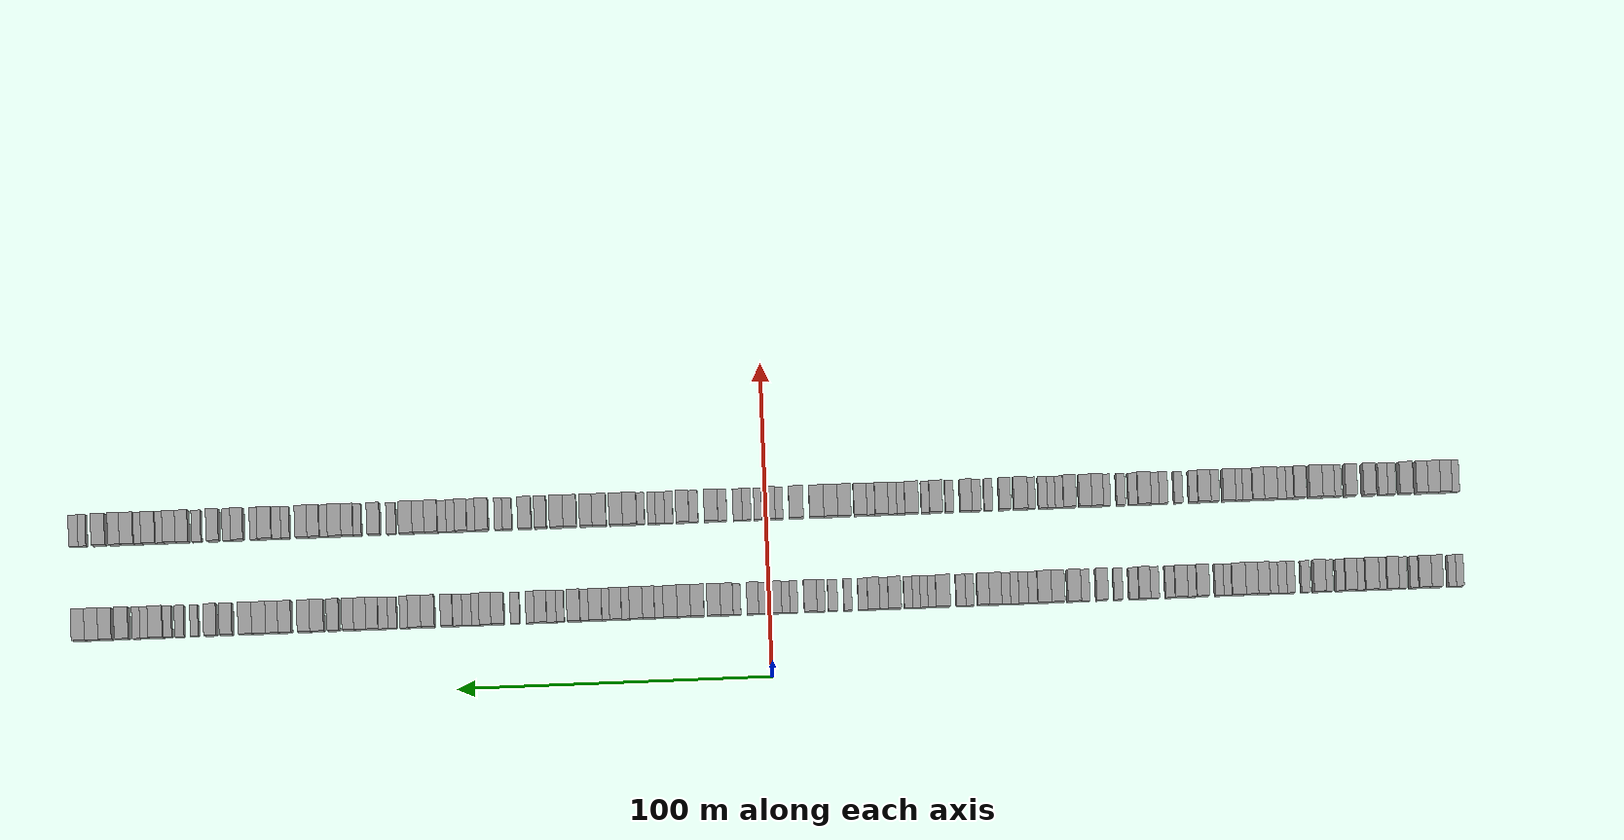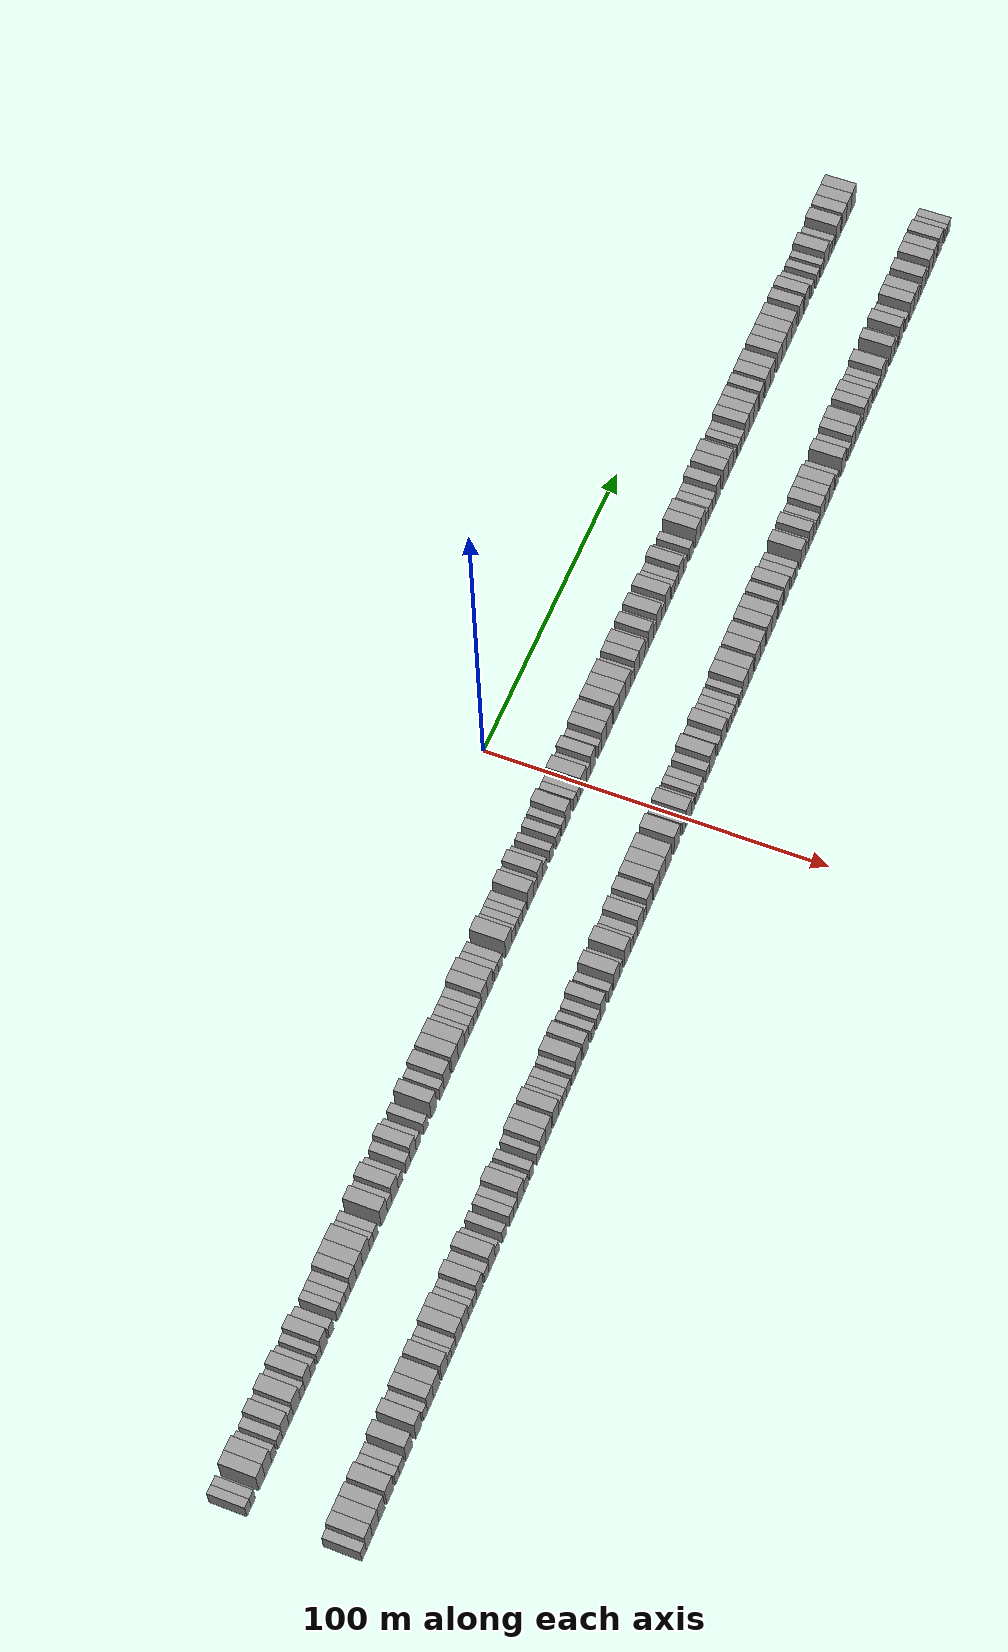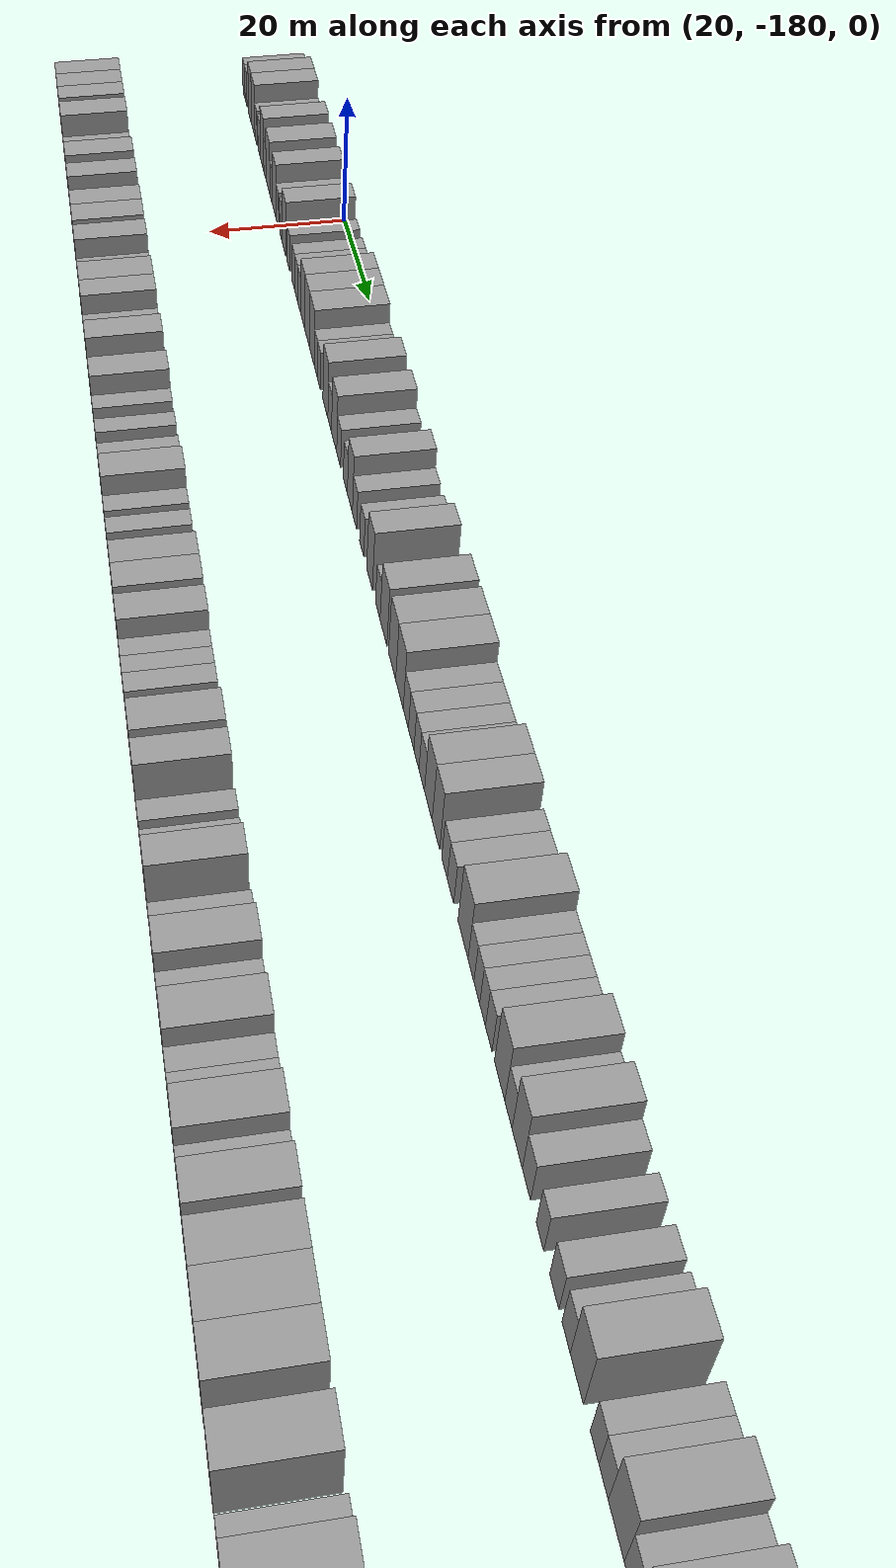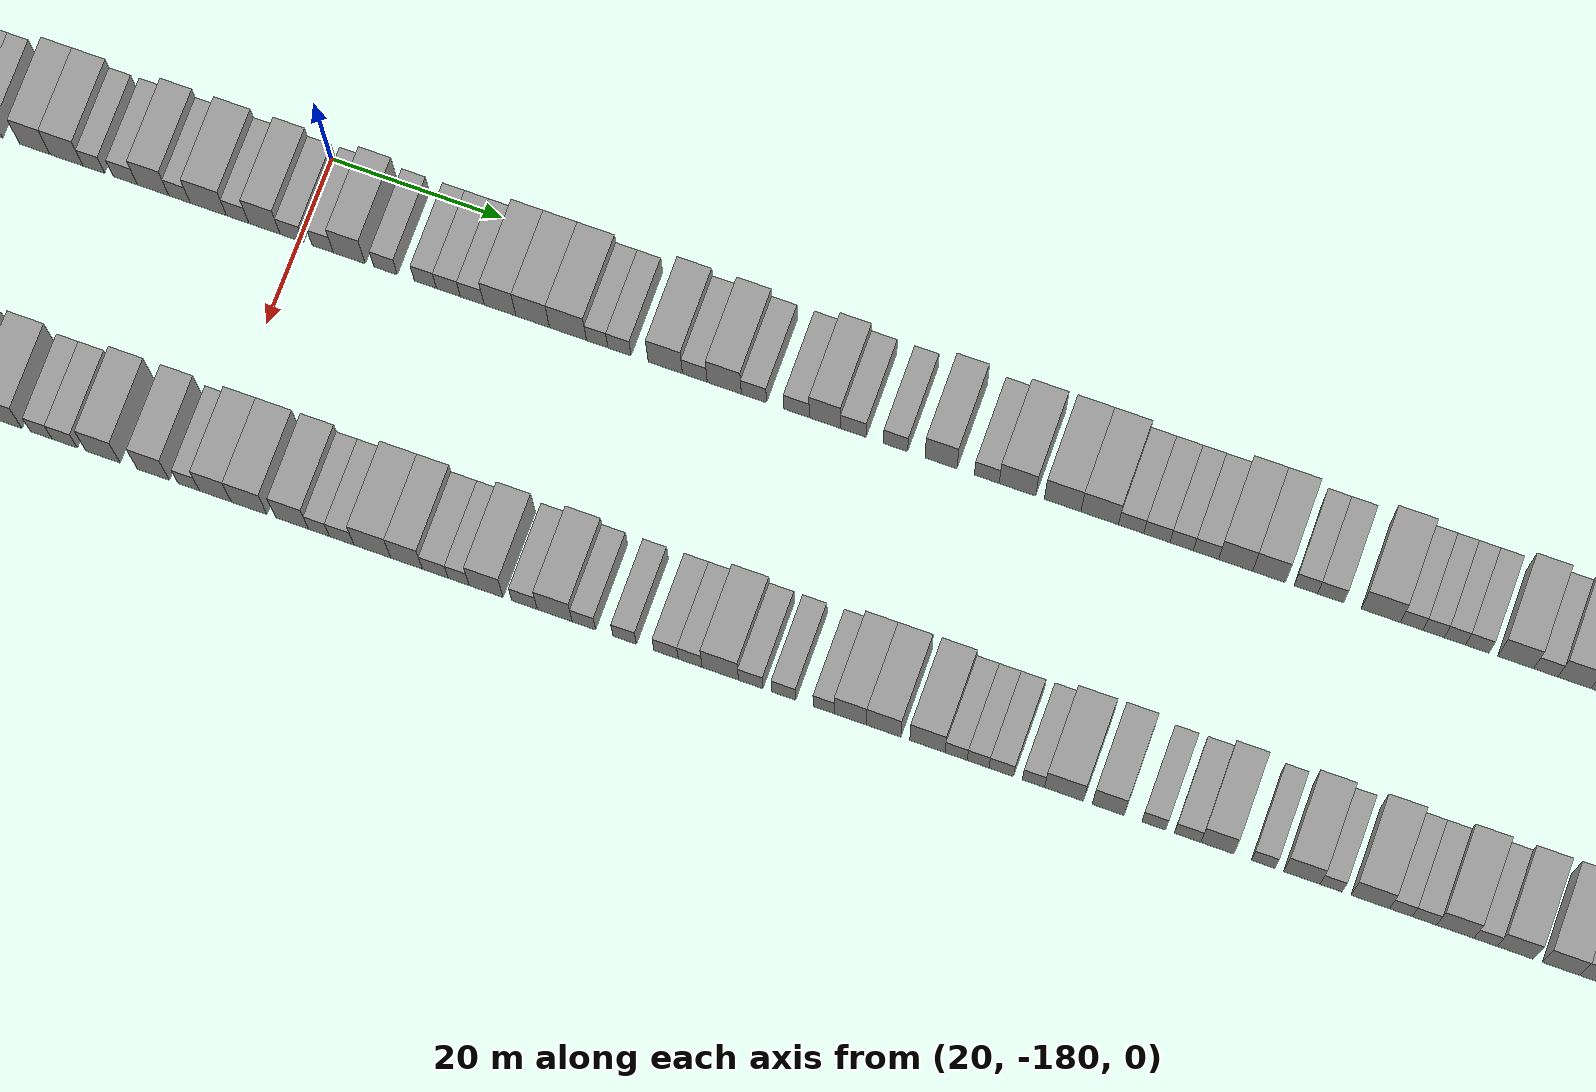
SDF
<sdf version="1.6">
 <world name="default">
  <scene>
   <sky><clouds><speed>12</speed></clouds></sky>
   <ambient>0.4 0.4 0.4 1</ambient>
   <background>0.7 0.7 0.7 1</background>
   <shadows>1</shadows>
  </scene>
  <gravity>0 0 -9.8066</gravity>
  <magnetic_field>6e-06 2.3e-05 -4.2e-05</magnetic_field>
  <physics default="0" name="default_physics" type="ode">
   <ode>
    <solver>
     <type>quick</type>
     <iters>10</iters>
     <sor>1.0</sor>
     <use_dynamic_moi_rescaling>0</use_dynamic_moi_rescaling>
    </solver>
    <constraints>
     <cfm>0</cfm>
     <erp>0.2</erp>
     <contact_max_correcting_vel>100</contact_max_correcting_vel>
     <contact_surface_layer>0.001</contact_surface_layer>
    </constraints>
   </ode>
   <max_step_size>0.004</max_step_size>
   <real_time_factor>1</real_time_factor>
   <real_time_update_rate>250</real_time_update_rate>
  </physics>
  <light name="sun" type="directional">
   <pose>0 0 10 0 0 0</pose>
   <diffuse>0.8 0.8 0.8 1</diffuse>
   <specular>0.2 0.2 0.2 1</specular>
   <attenuation>
    <range>1000</range>
    <constant>0.9</constant>
    <linear>0.01</linear>
    <quadratic>0.001</quadratic>
   </attenuation>
   <direction>-0.5 0.1 -0.9</direction>
  </light>
  <model name="building_1">
   <static>1</static>
   <pose>25.0000 -218.7724 0 0.000000 0.000000 0.000000</pose>
   <link name="link">
    <pose>0 0 3.00 0 0 0</pose>
    <collision name="collision"><geometry><box><size>10.0000 2.4552 6.0000</size></box></geometry></collision>
    <visual name="visual">
     <cast_shadows>0</cast_shadows>
     <geometry><box><size>10.0000 2.4552 6.0000</size></box></geometry>
     <material>
      <script>
       <uri>model://grey_wall/materials/scripts</uri>
       <uri>model://grey_wall/materials/textures</uri>
       <name>vrc/grey_wall</name>
      </script>
     </material>
    </visual>
   </link>
  </model>
  <model name="building_2">
   <static>1</static>
   <pose>25.0000 -216.3096 0 0.000000 0.000000 0.000000</pose>
   <link name="link">
    <pose>0 0 3.00 0 0 0</pose>
    <collision name="collision"><geometry><box><size>10.0000 2.4703 6.0000</size></box></geometry></collision>
    <visual name="visual">
     <cast_shadows>0</cast_shadows>
     <geometry><box><size>10.0000 2.4703 6.0000</size></box></geometry>
     <material>
      <script>
       <uri>model://grey_wall/materials/scripts</uri>
       <uri>model://grey_wall/materials/textures</uri>
       <name>vrc/grey_wall</name>
      </script>
     </material>
    </visual>
   </link>
  </model>
  <model name="building_3">
   <static>1</static>
   <pose>25.0000 -211.2696 0 0.000000 0.000000 0.000000</pose>
   <link name="link">
    <pose>0 0 4.50 0 0 0</pose>
    <collision name="collision"><geometry><box><size>10.0000 3.6098 9.0000</size></box></geometry></collision>
    <visual name="visual">
     <cast_shadows>0</cast_shadows>
     <geometry><box><size>10.0000 3.6098 9.0000</size></box></geometry>
     <material>
      <script>
       <uri>model://grey_wall/materials/scripts</uri>
       <uri>model://grey_wall/materials/textures</uri>
       <name>vrc/grey_wall</name>
      </script>
     </material>
    </visual>
   </link>
  </model>
  <model name="building_4">
   <static>1</static>
   <pose>25.0000 -207.5078 0 0.000000 0.000000 0.000000</pose>
   <link name="link">
    <pose>0 0 4.50 0 0 0</pose>
    <collision name="collision"><geometry><box><size>10.0000 3.9137 9.0000</size></box></geometry></collision>
    <visual name="visual">
     <cast_shadows>0</cast_shadows>
     <geometry><box><size>10.0000 3.9137 9.0000</size></box></geometry>
     <material>
      <script>
       <uri>model://grey_wall/materials/scripts</uri>
       <uri>model://grey_wall/materials/textures</uri>
       <name>vrc/grey_wall</name>
      </script>
     </material>
    </visual>
   </link>
  </model>
  <model name="building_5">
   <static>1</static>
   <pose>25.0000 -204.2752 0 0.000000 0.000000 0.000000</pose>
   <link name="link">
    <pose>0 0 3.00 0 0 0</pose>
    <collision name="collision"><geometry><box><size>10.0000 2.5516 6.0000</size></box></geometry></collision>
    <visual name="visual">
     <cast_shadows>0</cast_shadows>
     <geometry><box><size>10.0000 2.5516 6.0000</size></box></geometry>
     <material>
      <script>
       <uri>model://grey_wall/materials/scripts</uri>
       <uri>model://grey_wall/materials/textures</uri>
       <name>vrc/grey_wall</name>
      </script>
     </material>
    </visual>
   </link>
  </model>
  <model name="building_6">
   <static>1</static>
   <pose>25.0000 -200.5648 0 0.000000 0.000000 0.000000</pose>
   <link name="link">
    <pose>0 0 3.00 0 0 0</pose>
    <collision name="collision"><geometry><box><size>10.0000 2.8691 6.0000</size></box></geometry></collision>
    <visual name="visual">
     <cast_shadows>0</cast_shadows>
     <geometry><box><size>10.0000 2.8691 6.0000</size></box></geometry>
     <material>
      <script>
       <uri>model://grey_wall/materials/scripts</uri>
       <uri>model://grey_wall/materials/textures</uri>
       <name>vrc/grey_wall</name>
      </script>
     </material>
    </visual>
   </link>
  </model>
  <model name="building_7">
   <static>1</static>
   <pose>25.0000 -197.2733 0 0.000000 0.000000 0.000000</pose>
   <link name="link">
    <pose>0 0 4.50 0 0 0</pose>
    <collision name="collision"><geometry><box><size>10.0000 3.7139 9.0000</size></box></geometry></collision>
    <visual name="visual">
     <cast_shadows>0</cast_shadows>
     <geometry><box><size>10.0000 3.7139 9.0000</size></box></geometry>
     <material>
      <script>
       <uri>model://grey_wall/materials/scripts</uri>
       <uri>model://grey_wall/materials/textures</uri>
       <name>vrc/grey_wall</name>
      </script>
     </material>
    </visual>
   </link>
  </model>
  <model name="building_8">
   <static>1</static>
   <pose>25.0000 -194.1472 0 0.000000 0.000000 0.000000</pose>
   <link name="link">
    <pose>0 0 3.00 0 0 0</pose>
    <collision name="collision"><geometry><box><size>10.0000 2.5385 6.0000</size></box></geometry></collision>
    <visual name="visual">
     <cast_shadows>0</cast_shadows>
     <geometry><box><size>10.0000 2.5385 6.0000</size></box></geometry>
     <material>
      <script>
       <uri>model://grey_wall/materials/scripts</uri>
       <uri>model://grey_wall/materials/textures</uri>
       <name>vrc/grey_wall</name>
      </script>
     </material>
    </visual>
   </link>
  </model>
  <model name="building_9">
   <static>1</static>
   <pose>25.0000 -190.7358 0 0.000000 0.000000 0.000000</pose>
   <link name="link">
    <pose>0 0 4.50 0 0 0</pose>
    <collision name="collision"><geometry><box><size>10.0000 4.2843 9.0000</size></box></geometry></collision>
    <visual name="visual">
     <cast_shadows>0</cast_shadows>
     <geometry><box><size>10.0000 4.2843 9.0000</size></box></geometry>
     <material>
      <script>
       <uri>model://grey_wall/materials/scripts</uri>
       <uri>model://grey_wall/materials/textures</uri>
       <name>vrc/grey_wall</name>
      </script>
     </material>
    </visual>
   </link>
  </model>
  <model name="building_10">
   <static>1</static>
   <pose>25.0000 -187.2706 0 0.000000 0.000000 0.000000</pose>
   <link name="link">
    <pose>0 0 3.00 0 0 0</pose>
    <collision name="collision"><geometry><box><size>10.0000 2.6461 6.0000</size></box></geometry></collision>
    <visual name="visual">
     <cast_shadows>0</cast_shadows>
     <geometry><box><size>10.0000 2.6461 6.0000</size></box></geometry>
     <material>
      <script>
       <uri>model://grey_wall/materials/scripts</uri>
       <uri>model://grey_wall/materials/textures</uri>
       <name>vrc/grey_wall</name>
      </script>
     </material>
    </visual>
   </link>
  </model>
  <model name="building_11">
   <static>1</static>
   <pose>25.0000 -184.1075 0 0.000000 0.000000 0.000000</pose>
   <link name="link">
    <pose>0 0 4.50 0 0 0</pose>
    <collision name="collision"><geometry><box><size>10.0000 3.6802 9.0000</size></box></geometry></collision>
    <visual name="visual">
     <cast_shadows>0</cast_shadows>
     <geometry><box><size>10.0000 3.6802 9.0000</size></box></geometry>
     <material>
      <script>
       <uri>model://grey_wall/materials/scripts</uri>
       <uri>model://grey_wall/materials/textures</uri>
       <name>vrc/grey_wall</name>
      </script>
     </material>
    </visual>
   </link>
  </model>
  <model name="building_12">
   <static>1</static>
   <pose>25.0000 -180.8865 0 0.000000 0.000000 0.000000</pose>
   <link name="link">
    <pose>0 0 3.00 0 0 0</pose>
    <collision name="collision"><geometry><box><size>10.0000 2.7617 6.0000</size></box></geometry></collision>
    <visual name="visual">
     <cast_shadows>0</cast_shadows>
     <geometry><box><size>10.0000 2.7617 6.0000</size></box></geometry>
     <material>
      <script>
       <uri>model://grey_wall/materials/scripts</uri>
       <uri>model://grey_wall/materials/textures</uri>
       <name>vrc/grey_wall</name>
      </script>
     </material>
    </visual>
   </link>
  </model>
  <model name="building_13">
   <static>1</static>
   <pose>25.0000 -177.2530 0 0.000000 0.000000 0.000000</pose>
   <link name="link">
    <pose>0 0 3.00 0 0 0</pose>
    <collision name="collision"><geometry><box><size>10.0000 2.5054 6.0000</size></box></geometry></collision>
    <visual name="visual">
     <cast_shadows>0</cast_shadows>
     <geometry><box><size>10.0000 2.5054 6.0000</size></box></geometry>
     <material>
      <script>
       <uri>model://grey_wall/materials/scripts</uri>
       <uri>model://grey_wall/materials/textures</uri>
       <name>vrc/grey_wall</name>
      </script>
     </material>
    </visual>
   </link>
  </model>
  <model name="building_14">
   <static>1</static>
   <pose>25.0000 -174.1250 0 0.000000 0.000000 0.000000</pose>
   <link name="link">
    <pose>0 0 4.50 0 0 0</pose>
    <collision name="collision"><geometry><box><size>10.0000 3.7505 9.0000</size></box></geometry></collision>
    <visual name="visual">
     <cast_shadows>0</cast_shadows>
     <geometry><box><size>10.0000 3.7505 9.0000</size></box></geometry>
     <material>
      <script>
       <uri>model://grey_wall/materials/scripts</uri>
       <uri>model://grey_wall/materials/textures</uri>
       <name>vrc/grey_wall</name>
      </script>
     </material>
    </visual>
   </link>
  </model>
  <model name="building_15">
   <static>1</static>
   <pose>25.0000 -169.8699 0 0.000000 0.000000 0.000000</pose>
   <link name="link">
    <pose>0 0 3.00 0 0 0</pose>
    <collision name="collision"><geometry><box><size>10.0000 2.7595 6.0000</size></box></geometry></collision>
    <visual name="visual">
     <cast_shadows>0</cast_shadows>
     <geometry><box><size>10.0000 2.7595 6.0000</size></box></geometry>
     <material>
      <script>
       <uri>model://grey_wall/materials/scripts</uri>
       <uri>model://grey_wall/materials/textures</uri>
       <name>vrc/grey_wall</name>
      </script>
     </material>
    </visual>
   </link>
  </model>
  <model name="building_16">
   <static>1</static>
   <pose>25.0000 -165.1983 0 0.000000 0.000000 0.000000</pose>
   <link name="link">
    <pose>0 0 3.00 0 0 0</pose>
    <collision name="collision"><geometry><box><size>10.0000 2.5838 6.0000</size></box></geometry></collision>
    <visual name="visual">
     <cast_shadows>0</cast_shadows>
     <geometry><box><size>10.0000 2.5838 6.0000</size></box></geometry>
     <material>
      <script>
       <uri>model://grey_wall/materials/scripts</uri>
       <uri>model://grey_wall/materials/textures</uri>
       <name>vrc/grey_wall</name>
      </script>
     </material>
    </visual>
   </link>
  </model>
  <model name="building_17">
   <static>1</static>
   <pose>25.0000 -162.5082 0 0.000000 0.000000 0.000000</pose>
   <link name="link">
    <pose>0 0 3.00 0 0 0</pose>
    <collision name="collision"><geometry><box><size>10.0000 2.7964 6.0000</size></box></geometry></collision>
    <visual name="visual">
     <cast_shadows>0</cast_shadows>
     <geometry><box><size>10.0000 2.7964 6.0000</size></box></geometry>
     <material>
      <script>
       <uri>model://grey_wall/materials/scripts</uri>
       <uri>model://grey_wall/materials/textures</uri>
       <name>vrc/grey_wall</name>
      </script>
     </material>
    </visual>
   </link>
  </model>
  <model name="building_18">
   <static>1</static>
   <pose>25.0000 -159.7110 0 0.000000 0.000000 0.000000</pose>
   <link name="link">
    <pose>0 0 3.00 0 0 0</pose>
    <collision name="collision"><geometry><box><size>10.0000 2.7979 6.0000</size></box></geometry></collision>
    <visual name="visual">
     <cast_shadows>0</cast_shadows>
     <geometry><box><size>10.0000 2.7979 6.0000</size></box></geometry>
     <material>
      <script>
       <uri>model://grey_wall/materials/scripts</uri>
       <uri>model://grey_wall/materials/textures</uri>
       <name>vrc/grey_wall</name>
      </script>
     </material>
    </visual>
   </link>
  </model>
  <model name="building_19">
   <static>1</static>
   <pose>25.0000 -156.4629 0 0.000000 0.000000 0.000000</pose>
   <link name="link">
    <pose>0 0 4.50 0 0 0</pose>
    <collision name="collision"><geometry><box><size>10.0000 3.6983 9.0000</size></box></geometry></collision>
    <visual name="visual">
     <cast_shadows>0</cast_shadows>
     <geometry><box><size>10.0000 3.6983 9.0000</size></box></geometry>
     <material>
      <script>
       <uri>model://grey_wall/materials/scripts</uri>
       <uri>model://grey_wall/materials/textures</uri>
       <name>vrc/grey_wall</name>
      </script>
     </material>
    </visual>
   </link>
  </model>
  <model name="building_20">
   <static>1</static>
   <pose>25.0000 -152.6454 0 0.000000 0.000000 0.000000</pose>
   <link name="link">
    <pose>0 0 4.50 0 0 0</pose>
    <collision name="collision"><geometry><box><size>10.0000 3.9368 9.0000</size></box></geometry></collision>
    <visual name="visual">
     <cast_shadows>0</cast_shadows>
     <geometry><box><size>10.0000 3.9368 9.0000</size></box></geometry>
     <material>
      <script>
       <uri>model://grey_wall/materials/scripts</uri>
       <uri>model://grey_wall/materials/textures</uri>
       <name>vrc/grey_wall</name>
      </script>
     </material>
    </visual>
   </link>
  </model>
  <model name="building_21">
   <static>1</static>
   <pose>25.0000 -148.5193 0 0.000000 0.000000 0.000000</pose>
   <link name="link">
    <pose>0 0 4.50 0 0 0</pose>
    <collision name="collision"><geometry><box><size>10.0000 4.3155 9.0000</size></box></geometry></collision>
    <visual name="visual">
     <cast_shadows>0</cast_shadows>
     <geometry><box><size>10.0000 4.3155 9.0000</size></box></geometry>
     <material>
      <script>
       <uri>model://grey_wall/materials/scripts</uri>
       <uri>model://grey_wall/materials/textures</uri>
       <name>vrc/grey_wall</name>
      </script>
     </material>
    </visual>
   </link>
  </model>
  <model name="building_22">
   <static>1</static>
   <pose>25.0000 -145.1118 0 0.000000 0.000000 0.000000</pose>
   <link name="link">
    <pose>0 0 3.00 0 0 0</pose>
    <collision name="collision"><geometry><box><size>10.0000 2.4994 6.0000</size></box></geometry></collision>
    <visual name="visual">
     <cast_shadows>0</cast_shadows>
     <geometry><box><size>10.0000 2.4994 6.0000</size></box></geometry>
     <material>
      <script>
       <uri>model://grey_wall/materials/scripts</uri>
       <uri>model://grey_wall/materials/textures</uri>
       <name>vrc/grey_wall</name>
      </script>
     </material>
    </visual>
   </link>
  </model>
  <model name="building_23">
   <static>1</static>
   <pose>25.0000 -142.5120 0 0.000000 0.000000 0.000000</pose>
   <link name="link">
    <pose>0 0 3.00 0 0 0</pose>
    <collision name="collision"><geometry><box><size>10.0000 2.7002 6.0000</size></box></geometry></collision>
    <visual name="visual">
     <cast_shadows>0</cast_shadows>
     <geometry><box><size>10.0000 2.7002 6.0000</size></box></geometry>
     <material>
      <script>
       <uri>model://grey_wall/materials/scripts</uri>
       <uri>model://grey_wall/materials/textures</uri>
       <name>vrc/grey_wall</name>
      </script>
     </material>
    </visual>
   </link>
  </model>
  <model name="building_24">
   <static>1</static>
   <pose>25.0000 -137.1737 0 0.000000 0.000000 0.000000</pose>
   <link name="link">
    <pose>0 0 4.50 0 0 0</pose>
    <collision name="collision"><geometry><box><size>10.0000 3.9764 9.0000</size></box></geometry></collision>
    <visual name="visual">
     <cast_shadows>0</cast_shadows>
     <geometry><box><size>10.0000 3.9764 9.0000</size></box></geometry>
     <material>
      <script>
       <uri>model://grey_wall/materials/scripts</uri>
       <uri>model://grey_wall/materials/textures</uri>
       <name>vrc/grey_wall</name>
      </script>
     </material>
    </visual>
   </link>
  </model>
  <model name="building_25">
   <static>1</static>
   <pose>25.0000 -133.7473 0 0.000000 0.000000 0.000000</pose>
   <link name="link">
    <pose>0 0 3.00 0 0 0</pose>
    <collision name="collision"><geometry><box><size>10.0000 2.8764 6.0000</size></box></geometry></collision>
    <visual name="visual">
     <cast_shadows>0</cast_shadows>
     <geometry><box><size>10.0000 2.8764 6.0000</size></box></geometry>
     <material>
      <script>
       <uri>model://grey_wall/materials/scripts</uri>
       <uri>model://grey_wall/materials/textures</uri>
       <name>vrc/grey_wall</name>
      </script>
     </material>
    </visual>
   </link>
  </model>
  <model name="building_26">
   <static>1</static>
   <pose>25.0000 -130.3267 0 0.000000 0.000000 0.000000</pose>
   <link name="link">
    <pose>0 0 4.50 0 0 0</pose>
    <collision name="collision"><geometry><box><size>10.0000 3.9649 9.0000</size></box></geometry></collision>
    <visual name="visual">
     <cast_shadows>0</cast_shadows>
     <geometry><box><size>10.0000 3.9649 9.0000</size></box></geometry>
     <material>
      <script>
       <uri>model://grey_wall/materials/scripts</uri>
       <uri>model://grey_wall/materials/textures</uri>
       <name>vrc/grey_wall</name>
      </script>
     </material>
    </visual>
   </link>
  </model>
  <model name="building_27">
   <static>1</static>
   <pose>25.0000 -126.8843 0 0.000000 0.000000 0.000000</pose>
   <link name="link">
    <pose>0 0 3.00 0 0 0</pose>
    <collision name="collision"><geometry><box><size>10.0000 2.9198 6.0000</size></box></geometry></collision>
    <visual name="visual">
     <cast_shadows>0</cast_shadows>
     <geometry><box><size>10.0000 2.9198 6.0000</size></box></geometry>
     <material>
      <script>
       <uri>model://grey_wall/materials/scripts</uri>
       <uri>model://grey_wall/materials/textures</uri>
       <name>vrc/grey_wall</name>
      </script>
     </material>
    </visual>
   </link>
  </model>
  <model name="building_28">
   <static>1</static>
   <pose>25.0000 -121.9462 0 0.000000 0.000000 0.000000</pose>
   <link name="link">
    <pose>0 0 3.00 0 0 0</pose>
    <collision name="collision"><geometry><box><size>10.0000 2.9565 6.0000</size></box></geometry></collision>
    <visual name="visual">
     <cast_shadows>0</cast_shadows>
     <geometry><box><size>10.0000 2.9565 6.0000</size></box></geometry>
     <material>
      <script>
       <uri>model://grey_wall/materials/scripts</uri>
       <uri>model://grey_wall/materials/textures</uri>
       <name>vrc/grey_wall</name>
      </script>
     </material>
    </visual>
   </link>
  </model>
  <model name="building_29">
   <static>1</static>
   <pose>25.0000 -118.6565 0 0.000000 0.000000 0.000000</pose>
   <link name="link">
    <pose>0 0 4.50 0 0 0</pose>
    <collision name="collision"><geometry><box><size>10.0000 3.6229 9.0000</size></box></geometry></collision>
    <visual name="visual">
     <cast_shadows>0</cast_shadows>
     <geometry><box><size>10.0000 3.6229 9.0000</size></box></geometry>
     <material>
      <script>
       <uri>model://grey_wall/materials/scripts</uri>
       <uri>model://grey_wall/materials/textures</uri>
       <name>vrc/grey_wall</name>
      </script>
     </material>
    </visual>
   </link>
  </model>
  <model name="building_30">
   <static>1</static>
   <pose>25.0000 -115.3672 0 0.000000 0.000000 0.000000</pose>
   <link name="link">
    <pose>0 0 3.00 0 0 0</pose>
    <collision name="collision"><geometry><box><size>10.0000 2.9556 6.0000</size></box></geometry></collision>
    <visual name="visual">
     <cast_shadows>0</cast_shadows>
     <geometry><box><size>10.0000 2.9556 6.0000</size></box></geometry>
     <material>
      <script>
       <uri>model://grey_wall/materials/scripts</uri>
       <uri>model://grey_wall/materials/textures</uri>
       <name>vrc/grey_wall</name>
      </script>
     </material>
    </visual>
   </link>
  </model>
  <model name="building_31">
   <static>1</static>
   <pose>25.0000 -110.4916 0 0.000000 0.000000 0.000000</pose>
   <link name="link">
    <pose>0 0 3.00 0 0 0</pose>
    <collision name="collision"><geometry><box><size>10.0000 2.7957 6.0000</size></box></geometry></collision>
    <visual name="visual">
     <cast_shadows>0</cast_shadows>
     <geometry><box><size>10.0000 2.7957 6.0000</size></box></geometry>
     <material>
      <script>
       <uri>model://grey_wall/materials/scripts</uri>
       <uri>model://grey_wall/materials/textures</uri>
       <name>vrc/grey_wall</name>
      </script>
     </material>
    </visual>
   </link>
  </model>
  <model name="building_32">
   <static>1</static>
   <pose>25.0000 -105.2470 0 0.000000 0.000000 0.000000</pose>
   <link name="link">
    <pose>0 0 4.50 0 0 0</pose>
    <collision name="collision"><geometry><box><size>10.0000 3.6934 9.0000</size></box></geometry></collision>
    <visual name="visual">
     <cast_shadows>0</cast_shadows>
     <geometry><box><size>10.0000 3.6934 9.0000</size></box></geometry>
     <material>
      <script>
       <uri>model://grey_wall/materials/scripts</uri>
       <uri>model://grey_wall/materials/textures</uri>
       <name>vrc/grey_wall</name>
      </script>
     </material>
    </visual>
   </link>
  </model>
  <model name="building_33">
   <static>1</static>
   <pose>25.0000 -99.9704 0 0.000000 0.000000 0.000000</pose>
   <link name="link">
    <pose>0 0 3.00 0 0 0</pose>
    <collision name="collision"><geometry><box><size>10.0000 2.8598 6.0000</size></box></geometry></collision>
    <visual name="visual">
     <cast_shadows>0</cast_shadows>
     <geometry><box><size>10.0000 2.8598 6.0000</size></box></geometry>
     <material>
      <script>
       <uri>model://grey_wall/materials/scripts</uri>
       <uri>model://grey_wall/materials/textures</uri>
       <name>vrc/grey_wall</name>
      </script>
     </material>
    </visual>
   </link>
  </model>
  <model name="building_34">
   <static>1</static>
   <pose>25.0000 -96.4412 0 0.000000 0.000000 0.000000</pose>
   <link name="link">
    <pose>0 0 4.50 0 0 0</pose>
    <collision name="collision"><geometry><box><size>10.0000 4.1985 9.0000</size></box></geometry></collision>
    <visual name="visual">
     <cast_shadows>0</cast_shadows>
     <geometry><box><size>10.0000 4.1985 9.0000</size></box></geometry>
     <material>
      <script>
       <uri>model://grey_wall/materials/scripts</uri>
       <uri>model://grey_wall/materials/textures</uri>
       <name>vrc/grey_wall</name>
      </script>
     </material>
    </visual>
   </link>
  </model>
  <model name="building_35">
   <static>1</static>
   <pose>25.0000 -91.2373 0 0.000000 0.000000 0.000000</pose>
   <link name="link">
    <pose>0 0 4.50 0 0 0</pose>
    <collision name="collision"><geometry><box><size>10.0000 4.2094 9.0000</size></box></geometry></collision>
    <visual name="visual">
     <cast_shadows>0</cast_shadows>
     <geometry><box><size>10.0000 4.2094 9.0000</size></box></geometry>
     <material>
      <script>
       <uri>model://grey_wall/materials/scripts</uri>
       <uri>model://grey_wall/materials/textures</uri>
       <name>vrc/grey_wall</name>
      </script>
     </material>
    </visual>
   </link>
  </model>
  <model name="building_36">
   <static>1</static>
   <pose>25.0000 -86.9790 0 0.000000 0.000000 0.000000</pose>
   <link name="link">
    <pose>0 0 4.50 0 0 0</pose>
    <collision name="collision"><geometry><box><size>10.0000 4.3072 9.0000</size></box></geometry></collision>
    <visual name="visual">
     <cast_shadows>0</cast_shadows>
     <geometry><box><size>10.0000 4.3072 9.0000</size></box></geometry>
     <material>
      <script>
       <uri>model://grey_wall/materials/scripts</uri>
       <uri>model://grey_wall/materials/textures</uri>
       <name>vrc/grey_wall</name>
      </script>
     </material>
    </visual>
   </link>
  </model>
  <model name="building_37">
   <static>1</static>
   <pose>25.0000 -83.3765 0 0.000000 0.000000 0.000000</pose>
   <link name="link">
    <pose>0 0 3.00 0 0 0</pose>
    <collision name="collision"><geometry><box><size>10.0000 2.8978 6.0000</size></box></geometry></collision>
    <visual name="visual">
     <cast_shadows>0</cast_shadows>
     <geometry><box><size>10.0000 2.8978 6.0000</size></box></geometry>
     <material>
      <script>
       <uri>model://grey_wall/materials/scripts</uri>
       <uri>model://grey_wall/materials/textures</uri>
       <name>vrc/grey_wall</name>
      </script>
     </material>
    </visual>
   </link>
  </model>
  <model name="building_38">
   <static>1</static>
   <pose>25.0000 -80.4277 0 0.000000 0.000000 0.000000</pose>
   <link name="link">
    <pose>0 0 3.00 0 0 0</pose>
    <collision name="collision"><geometry><box><size>10.0000 2.9997 6.0000</size></box></geometry></collision>
    <visual name="visual">
     <cast_shadows>0</cast_shadows>
     <geometry><box><size>10.0000 2.9997 6.0000</size></box></geometry>
     <material>
      <script>
       <uri>model://grey_wall/materials/scripts</uri>
       <uri>model://grey_wall/materials/textures</uri>
       <name>vrc/grey_wall</name>
      </script>
     </material>
    </visual>
   </link>
  </model>
  <model name="building_39">
   <static>1</static>
   <pose>25.0000 -77.5892 0 0.000000 0.000000 0.000000</pose>
   <link name="link">
    <pose>0 0 3.00 0 0 0</pose>
    <collision name="collision"><geometry><box><size>10.0000 2.6772 6.0000</size></box></geometry></collision>
    <visual name="visual">
     <cast_shadows>0</cast_shadows>
     <geometry><box><size>10.0000 2.6772 6.0000</size></box></geometry>
     <material>
      <script>
       <uri>model://grey_wall/materials/scripts</uri>
       <uri>model://grey_wall/materials/textures</uri>
       <name>vrc/grey_wall</name>
      </script>
     </material>
    </visual>
   </link>
  </model>
  <model name="building_40">
   <static>1</static>
   <pose>25.0000 -74.8077 0 0.000000 0.000000 0.000000</pose>
   <link name="link">
    <pose>0 0 3.00 0 0 0</pose>
    <collision name="collision"><geometry><box><size>10.0000 2.8858 6.0000</size></box></geometry></collision>
    <visual name="visual">
     <cast_shadows>0</cast_shadows>
     <geometry><box><size>10.0000 2.8858 6.0000</size></box></geometry>
     <material>
      <script>
       <uri>model://grey_wall/materials/scripts</uri>
       <uri>model://grey_wall/materials/textures</uri>
       <name>vrc/grey_wall</name>
      </script>
     </material>
    </visual>
   </link>
  </model>
  <model name="building_41">
   <static>1</static>
   <pose>25.0000 -71.4150 0 0.000000 0.000000 0.000000</pose>
   <link name="link">
    <pose>0 0 4.50 0 0 0</pose>
    <collision name="collision"><geometry><box><size>10.0000 3.8998 9.0000</size></box></geometry></collision>
    <visual name="visual">
     <cast_shadows>0</cast_shadows>
     <geometry><box><size>10.0000 3.8998 9.0000</size></box></geometry>
     <material>
      <script>
       <uri>model://grey_wall/materials/scripts</uri>
       <uri>model://grey_wall/materials/textures</uri>
       <name>vrc/grey_wall</name>
      </script>
     </material>
    </visual>
   </link>
  </model>
  <model name="building_42">
   <static>1</static>
   <pose>25.0000 -67.5965 0 0.000000 0.000000 0.000000</pose>
   <link name="link">
    <pose>0 0 4.50 0 0 0</pose>
    <collision name="collision"><geometry><box><size>10.0000 3.7373 9.0000</size></box></geometry></collision>
    <visual name="visual">
     <cast_shadows>0</cast_shadows>
     <geometry><box><size>10.0000 3.7373 9.0000</size></box></geometry>
     <material>
      <script>
       <uri>model://grey_wall/materials/scripts</uri>
       <uri>model://grey_wall/materials/textures</uri>
       <name>vrc/grey_wall</name>
      </script>
     </material>
    </visual>
   </link>
  </model>
  <model name="building_43">
   <static>1</static>
   <pose>25.0000 -63.3941 0 0.000000 0.000000 0.000000</pose>
   <link name="link">
    <pose>0 0 3.00 0 0 0</pose>
    <collision name="collision"><geometry><box><size>10.0000 2.6675 6.0000</size></box></geometry></collision>
    <visual name="visual">
     <cast_shadows>0</cast_shadows>
     <geometry><box><size>10.0000 2.6675 6.0000</size></box></geometry>
     <material>
      <script>
       <uri>model://grey_wall/materials/scripts</uri>
       <uri>model://grey_wall/materials/textures</uri>
       <name>vrc/grey_wall</name>
      </script>
     </material>
    </visual>
   </link>
  </model>
  <model name="building_44">
   <static>1</static>
   <pose>25.0000 -60.5733 0 0.000000 0.000000 0.000000</pose>
   <link name="link">
    <pose>0 0 3.00 0 0 0</pose>
    <collision name="collision"><geometry><box><size>10.0000 2.9741 6.0000</size></box></geometry></collision>
    <visual name="visual">
     <cast_shadows>0</cast_shadows>
     <geometry><box><size>10.0000 2.9741 6.0000</size></box></geometry>
     <material>
      <script>
       <uri>model://grey_wall/materials/scripts</uri>
       <uri>model://grey_wall/materials/textures</uri>
       <name>vrc/grey_wall</name>
      </script>
     </material>
    </visual>
   </link>
  </model>
  <model name="building_45">
   <static>1</static>
   <pose>25.0000 -54.8573 0 0.000000 0.000000 0.000000</pose>
   <link name="link">
    <pose>0 0 4.50 0 0 0</pose>
    <collision name="collision"><geometry><box><size>10.0000 4.4580 9.0000</size></box></geometry></collision>
    <visual name="visual">
     <cast_shadows>0</cast_shadows>
     <geometry><box><size>10.0000 4.4580 9.0000</size></box></geometry>
     <material>
      <script>
       <uri>model://grey_wall/materials/scripts</uri>
       <uri>model://grey_wall/materials/textures</uri>
       <name>vrc/grey_wall</name>
      </script>
     </material>
    </visual>
   </link>
  </model>
  <model name="building_46">
   <static>1</static>
   <pose>25.0000 -51.3560 0 0.000000 0.000000 0.000000</pose>
   <link name="link">
    <pose>0 0 3.00 0 0 0</pose>
    <collision name="collision"><geometry><box><size>10.0000 2.5446 6.0000</size></box></geometry></collision>
    <visual name="visual">
     <cast_shadows>0</cast_shadows>
     <geometry><box><size>10.0000 2.5446 6.0000</size></box></geometry>
     <material>
      <script>
       <uri>model://grey_wall/materials/scripts</uri>
       <uri>model://grey_wall/materials/textures</uri>
       <name>vrc/grey_wall</name>
      </script>
     </material>
    </visual>
   </link>
  </model>
  <model name="building_47">
   <static>1</static>
   <pose>25.0000 -48.8623 0 0.000000 0.000000 0.000000</pose>
   <link name="link">
    <pose>0 0 3.00 0 0 0</pose>
    <collision name="collision"><geometry><box><size>10.0000 2.4429 6.0000</size></box></geometry></collision>
    <visual name="visual">
     <cast_shadows>0</cast_shadows>
     <geometry><box><size>10.0000 2.4429 6.0000</size></box></geometry>
     <material>
      <script>
       <uri>model://grey_wall/materials/scripts</uri>
       <uri>model://grey_wall/materials/textures</uri>
       <name>vrc/grey_wall</name>
      </script>
     </material>
    </visual>
   </link>
  </model>
  <model name="building_48">
   <static>1</static>
   <pose>25.0000 -46.4388 0 0.000000 0.000000 0.000000</pose>
   <link name="link">
    <pose>0 0 3.00 0 0 0</pose>
    <collision name="collision"><geometry><box><size>10.0000 2.4039 6.0000</size></box></geometry></collision>
    <visual name="visual">
     <cast_shadows>0</cast_shadows>
     <geometry><box><size>10.0000 2.4039 6.0000</size></box></geometry>
     <material>
      <script>
       <uri>model://grey_wall/materials/scripts</uri>
       <uri>model://grey_wall/materials/textures</uri>
       <name>vrc/grey_wall</name>
      </script>
     </material>
    </visual>
   </link>
  </model>
  <model name="building_49">
   <static>1</static>
   <pose>25.0000 -43.9064 0 0.000000 0.000000 0.000000</pose>
   <link name="link">
    <pose>0 0 3.00 0 0 0</pose>
    <collision name="collision"><geometry><box><size>10.0000 2.6609 6.0000</size></box></geometry></collision>
    <visual name="visual">
     <cast_shadows>0</cast_shadows>
     <geometry><box><size>10.0000 2.6609 6.0000</size></box></geometry>
     <material>
      <script>
       <uri>model://grey_wall/materials/scripts</uri>
       <uri>model://grey_wall/materials/textures</uri>
       <name>vrc/grey_wall</name>
      </script>
     </material>
    </visual>
   </link>
  </model>
  <model name="building_50">
   <static>1</static>
   <pose>25.0000 -39.5402 0 0.000000 0.000000 0.000000</pose>
   <link name="link">
    <pose>0 0 4.50 0 0 0</pose>
    <collision name="collision"><geometry><box><size>10.0000 4.0715 9.0000</size></box></geometry></collision>
    <visual name="visual">
     <cast_shadows>0</cast_shadows>
     <geometry><box><size>10.0000 4.0715 9.0000</size></box></geometry>
     <material>
      <script>
       <uri>model://grey_wall/materials/scripts</uri>
       <uri>model://grey_wall/materials/textures</uri>
       <name>vrc/grey_wall</name>
      </script>
     </material>
    </visual>
   </link>
  </model>
  <model name="building_51">
   <static>1</static>
   <pose>25.0000 -36.1357 0 0.000000 0.000000 0.000000</pose>
   <link name="link">
    <pose>0 0 3.00 0 0 0</pose>
    <collision name="collision"><geometry><box><size>10.0000 2.7375 6.0000</size></box></geometry></collision>
    <visual name="visual">
     <cast_shadows>0</cast_shadows>
     <geometry><box><size>10.0000 2.7375 6.0000</size></box></geometry>
     <material>
      <script>
       <uri>model://grey_wall/materials/scripts</uri>
       <uri>model://grey_wall/materials/textures</uri>
       <name>vrc/grey_wall</name>
      </script>
     </material>
    </visual>
   </link>
  </model>
  <model name="building_52">
   <static>1</static>
   <pose>25.0000 -32.8725 0 0.000000 0.000000 0.000000</pose>
   <link name="link">
    <pose>0 0 4.50 0 0 0</pose>
    <collision name="collision"><geometry><box><size>10.0000 3.7889 9.0000</size></box></geometry></collision>
    <visual name="visual">
     <cast_shadows>0</cast_shadows>
     <geometry><box><size>10.0000 3.7889 9.0000</size></box></geometry>
     <material>
      <script>
       <uri>model://grey_wall/materials/scripts</uri>
       <uri>model://grey_wall/materials/textures</uri>
       <name>vrc/grey_wall</name>
      </script>
     </material>
    </visual>
   </link>
  </model>
  <model name="building_53">
   <static>1</static>
   <pose>25.0000 -29.5066 0 0.000000 0.000000 0.000000</pose>
   <link name="link">
    <pose>0 0 3.00 0 0 0</pose>
    <collision name="collision"><geometry><box><size>10.0000 2.9428 6.0000</size></box></geometry></collision>
    <visual name="visual">
     <cast_shadows>0</cast_shadows>
     <geometry><box><size>10.0000 2.9428 6.0000</size></box></geometry>
     <material>
      <script>
       <uri>model://grey_wall/materials/scripts</uri>
       <uri>model://grey_wall/materials/textures</uri>
       <name>vrc/grey_wall</name>
      </script>
     </material>
    </visual>
   </link>
  </model>
  <model name="building_54">
   <static>1</static>
   <pose>25.0000 -24.7598 0 0.000000 0.000000 0.000000</pose>
   <link name="link">
    <pose>0 0 3.00 0 0 0</pose>
    <collision name="collision"><geometry><box><size>10.0000 2.5508 6.0000</size></box></geometry></collision>
    <visual name="visual">
     <cast_shadows>0</cast_shadows>
     <geometry><box><size>10.0000 2.5508 6.0000</size></box></geometry>
     <material>
      <script>
       <uri>model://grey_wall/materials/scripts</uri>
       <uri>model://grey_wall/materials/textures</uri>
       <name>vrc/grey_wall</name>
      </script>
     </material>
    </visual>
   </link>
  </model>
  <model name="building_55">
   <static>1</static>
   <pose>25.0000 -19.9886 0 0.000000 0.000000 0.000000</pose>
   <link name="link">
    <pose>0 0 3.00 0 0 0</pose>
    <collision name="collision"><geometry><box><size>10.0000 2.9917 6.0000</size></box></geometry></collision>
    <visual name="visual">
     <cast_shadows>0</cast_shadows>
     <geometry><box><size>10.0000 2.9917 6.0000</size></box></geometry>
     <material>
      <script>
       <uri>model://grey_wall/materials/scripts</uri>
       <uri>model://grey_wall/materials/textures</uri>
       <name>vrc/grey_wall</name>
      </script>
     </material>
    </visual>
   </link>
  </model>
  <model name="building_56">
   <static>1</static>
   <pose>25.0000 -16.1954 0 0.000000 0.000000 0.000000</pose>
   <link name="link">
    <pose>0 0 3.00 0 0 0</pose>
    <collision name="collision"><geometry><box><size>10.0000 2.5946 6.0000</size></box></geometry></collision>
    <visual name="visual">
     <cast_shadows>0</cast_shadows>
     <geometry><box><size>10.0000 2.5946 6.0000</size></box></geometry>
     <material>
      <script>
       <uri>model://grey_wall/materials/scripts</uri>
       <uri>model://grey_wall/materials/textures</uri>
       <name>vrc/grey_wall</name>
      </script>
     </material>
    </visual>
   </link>
  </model>
  <model name="building_57">
   <static>1</static>
   <pose>25.0000 -12.8739 0 0.000000 0.000000 0.000000</pose>
   <link name="link">
    <pose>0 0 4.50 0 0 0</pose>
    <collision name="collision"><geometry><box><size>10.0000 4.0484 9.0000</size></box></geometry></collision>
    <visual name="visual">
     <cast_shadows>0</cast_shadows>
     <geometry><box><size>10.0000 4.0484 9.0000</size></box></geometry>
     <material>
      <script>
       <uri>model://grey_wall/materials/scripts</uri>
       <uri>model://grey_wall/materials/textures</uri>
       <name>vrc/grey_wall</name>
      </script>
     </material>
    </visual>
   </link>
  </model>
  <model name="building_58">
   <static>1</static>
   <pose>25.0000 -7.5938 0 0.000000 0.000000 0.000000</pose>
   <link name="link">
    <pose>0 0 3.00 0 0 0</pose>
    <collision name="collision"><geometry><box><size>10.0000 2.5119 6.0000</size></box></geometry></collision>
    <visual name="visual">
     <cast_shadows>0</cast_shadows>
     <geometry><box><size>10.0000 2.5119 6.0000</size></box></geometry>
     <material>
      <script>
       <uri>model://grey_wall/materials/scripts</uri>
       <uri>model://grey_wall/materials/textures</uri>
       <name>vrc/grey_wall</name>
      </script>
     </material>
    </visual>
   </link>
  </model>
  <model name="building_59">
   <static>1</static>
   <pose>25.0000 -5.0387 0 0.000000 0.000000 0.000000</pose>
   <link name="link">
    <pose>0 0 3.00 0 0 0</pose>
    <collision name="collision"><geometry><box><size>10.0000 2.5984 6.0000</size></box></geometry></collision>
    <visual name="visual">
     <cast_shadows>0</cast_shadows>
     <geometry><box><size>10.0000 2.5984 6.0000</size></box></geometry>
     <material>
      <script>
       <uri>model://grey_wall/materials/scripts</uri>
       <uri>model://grey_wall/materials/textures</uri>
       <name>vrc/grey_wall</name>
      </script>
     </material>
    </visual>
   </link>
  </model>
  <model name="building_60">
   <static>1</static>
   <pose>25.0000 -1.5689 0 0.000000 0.000000 0.000000</pose>
   <link name="link">
    <pose>0 0 4.50 0 0 0</pose>
    <collision name="collision"><geometry><box><size>10.0000 4.3411 9.0000</size></box></geometry></collision>
    <visual name="visual">
     <cast_shadows>0</cast_shadows>
     <geometry><box><size>10.0000 4.3411 9.0000</size></box></geometry>
     <material>
      <script>
       <uri>model://grey_wall/materials/scripts</uri>
       <uri>model://grey_wall/materials/textures</uri>
       <name>vrc/grey_wall</name>
      </script>
     </material>
    </visual>
   </link>
  </model>
  <model name="building_61">
   <static>1</static>
   <pose>25.0000 2.0888 0 0.000000 0.000000 0.000000</pose>
   <link name="link">
    <pose>0 0 3.00 0 0 0</pose>
    <collision name="collision"><geometry><box><size>10.0000 2.9745 6.0000</size></box></geometry></collision>
    <visual name="visual">
     <cast_shadows>0</cast_shadows>
     <geometry><box><size>10.0000 2.9745 6.0000</size></box></geometry>
     <material>
      <script>
       <uri>model://grey_wall/materials/scripts</uri>
       <uri>model://grey_wall/materials/textures</uri>
       <name>vrc/grey_wall</name>
      </script>
     </material>
    </visual>
   </link>
  </model>
  <model name="building_62">
   <static>1</static>
   <pose>25.0000 5.4020 0 0.000000 0.000000 0.000000</pose>
   <link name="link">
    <pose>0 0 4.50 0 0 0</pose>
    <collision name="collision"><geometry><box><size>10.0000 3.6519 9.0000</size></box></geometry></collision>
    <visual name="visual">
     <cast_shadows>0</cast_shadows>
     <geometry><box><size>10.0000 3.6519 9.0000</size></box></geometry>
     <material>
      <script>
       <uri>model://grey_wall/materials/scripts</uri>
       <uri>model://grey_wall/materials/textures</uri>
       <name>vrc/grey_wall</name>
      </script>
     </material>
    </visual>
   </link>
  </model>
  <model name="building_63">
   <static>1</static>
   <pose>25.0000 10.4590 0 0.000000 0.000000 0.000000</pose>
   <link name="link">
    <pose>0 0 3.00 0 0 0</pose>
    <collision name="collision"><geometry><box><size>10.0000 2.4620 6.0000</size></box></geometry></collision>
    <visual name="visual">
     <cast_shadows>0</cast_shadows>
     <geometry><box><size>10.0000 2.4620 6.0000</size></box></geometry>
     <material>
      <script>
       <uri>model://grey_wall/materials/scripts</uri>
       <uri>model://grey_wall/materials/textures</uri>
       <name>vrc/grey_wall</name>
      </script>
     </material>
    </visual>
   </link>
  </model>
  <model name="building_64">
   <static>1</static>
   <pose>25.0000 13.6569 0 0.000000 0.000000 0.000000</pose>
   <link name="link">
    <pose>0 0 4.50 0 0 0</pose>
    <collision name="collision"><geometry><box><size>10.0000 3.9337 9.0000</size></box></geometry></collision>
    <visual name="visual">
     <cast_shadows>0</cast_shadows>
     <geometry><box><size>10.0000 3.9337 9.0000</size></box></geometry>
     <material>
      <script>
       <uri>model://grey_wall/materials/scripts</uri>
       <uri>model://grey_wall/materials/textures</uri>
       <name>vrc/grey_wall</name>
      </script>
     </material>
    </visual>
   </link>
  </model>
  <model name="building_65">
   <static>1</static>
   <pose>25.0000 17.7492 0 0.000000 0.000000 0.000000</pose>
   <link name="link">
    <pose>0 0 4.50 0 0 0</pose>
    <collision name="collision"><geometry><box><size>10.0000 4.2509 9.0000</size></box></geometry></collision>
    <visual name="visual">
     <cast_shadows>0</cast_shadows>
     <geometry><box><size>10.0000 4.2509 9.0000</size></box></geometry>
     <material>
      <script>
       <uri>model://grey_wall/materials/scripts</uri>
       <uri>model://grey_wall/materials/textures</uri>
       <name>vrc/grey_wall</name>
      </script>
     </material>
    </visual>
   </link>
  </model>
  <model name="building_66">
   <static>1</static>
   <pose>25.0000 23.0106 0 0.000000 0.000000 0.000000</pose>
   <link name="link">
    <pose>0 0 4.50 0 0 0</pose>
    <collision name="collision"><geometry><box><size>10.0000 4.2719 9.0000</size></box></geometry></collision>
    <visual name="visual">
     <cast_shadows>0</cast_shadows>
     <geometry><box><size>10.0000 4.2719 9.0000</size></box></geometry>
     <material>
      <script>
       <uri>model://grey_wall/materials/scripts</uri>
       <uri>model://grey_wall/materials/textures</uri>
       <name>vrc/grey_wall</name>
      </script>
     </material>
    </visual>
   </link>
  </model>
  <model name="building_67">
   <static>1</static>
   <pose>25.0000 27.2440 0 0.000000 0.000000 0.000000</pose>
   <link name="link">
    <pose>0 0 4.50 0 0 0</pose>
    <collision name="collision"><geometry><box><size>10.0000 4.1949 9.0000</size></box></geometry></collision>
    <visual name="visual">
     <cast_shadows>0</cast_shadows>
     <geometry><box><size>10.0000 4.1949 9.0000</size></box></geometry>
     <material>
      <script>
       <uri>model://grey_wall/materials/scripts</uri>
       <uri>model://grey_wall/materials/textures</uri>
       <name>vrc/grey_wall</name>
      </script>
     </material>
    </visual>
   </link>
  </model>
  <model name="building_68">
   <static>1</static>
   <pose>25.0000 31.5443 0 0.000000 0.000000 0.000000</pose>
   <link name="link">
    <pose>0 0 4.50 0 0 0</pose>
    <collision name="collision"><geometry><box><size>10.0000 4.4057 9.0000</size></box></geometry></collision>
    <visual name="visual">
     <cast_shadows>0</cast_shadows>
     <geometry><box><size>10.0000 4.4057 9.0000</size></box></geometry>
     <material>
      <script>
       <uri>model://grey_wall/materials/scripts</uri>
       <uri>model://grey_wall/materials/textures</uri>
       <name>vrc/grey_wall</name>
      </script>
     </material>
    </visual>
   </link>
  </model>
  <model name="building_69">
   <static>1</static>
   <pose>25.0000 35.1485 0 0.000000 0.000000 0.000000</pose>
   <link name="link">
    <pose>0 0 3.00 0 0 0</pose>
    <collision name="collision"><geometry><box><size>10.0000 2.8026 6.0000</size></box></geometry></collision>
    <visual name="visual">
     <cast_shadows>0</cast_shadows>
     <geometry><box><size>10.0000 2.8026 6.0000</size></box></geometry>
     <material>
      <script>
       <uri>model://grey_wall/materials/scripts</uri>
       <uri>model://grey_wall/materials/textures</uri>
       <name>vrc/grey_wall</name>
      </script>
     </material>
    </visual>
   </link>
  </model>
  <model name="building_70">
   <static>1</static>
   <pose>25.0000 38.4346 0 0.000000 0.000000 0.000000</pose>
   <link name="link">
    <pose>0 0 4.50 0 0 0</pose>
    <collision name="collision"><geometry><box><size>10.0000 3.7697 9.0000</size></box></geometry></collision>
    <visual name="visual">
     <cast_shadows>0</cast_shadows>
     <geometry><box><size>10.0000 3.7697 9.0000</size></box></geometry>
     <material>
      <script>
       <uri>model://grey_wall/materials/scripts</uri>
       <uri>model://grey_wall/materials/textures</uri>
       <name>vrc/grey_wall</name>
      </script>
     </material>
    </visual>
   </link>
  </model>
  <model name="building_71">
   <static>1</static>
   <pose>25.0000 42.3894 0 0.000000 0.000000 0.000000</pose>
   <link name="link">
    <pose>0 0 4.50 0 0 0</pose>
    <collision name="collision"><geometry><box><size>10.0000 4.1398 9.0000</size></box></geometry></collision>
    <visual name="visual">
     <cast_shadows>0</cast_shadows>
     <geometry><box><size>10.0000 4.1398 9.0000</size></box></geometry>
     <material>
      <script>
       <uri>model://grey_wall/materials/scripts</uri>
       <uri>model://grey_wall/materials/textures</uri>
       <name>vrc/grey_wall</name>
      </script>
     </material>
    </visual>
   </link>
  </model>
  <model name="building_72">
   <static>1</static>
   <pose>25.0000 45.7347 0 0.000000 0.000000 0.000000</pose>
   <link name="link">
    <pose>0 0 3.00 0 0 0</pose>
    <collision name="collision"><geometry><box><size>10.0000 2.5509 6.0000</size></box></geometry></collision>
    <visual name="visual">
     <cast_shadows>0</cast_shadows>
     <geometry><box><size>10.0000 2.5509 6.0000</size></box></geometry>
     <material>
      <script>
       <uri>model://grey_wall/materials/scripts</uri>
       <uri>model://grey_wall/materials/textures</uri>
       <name>vrc/grey_wall</name>
      </script>
     </material>
    </visual>
   </link>
  </model>
  <model name="building_73">
   <static>1</static>
   <pose>25.0000 48.8990 0 0.000000 0.000000 0.000000</pose>
   <link name="link">
    <pose>0 0 4.50 0 0 0</pose>
    <collision name="collision"><geometry><box><size>10.0000 3.7776 9.0000</size></box></geometry></collision>
    <visual name="visual">
     <cast_shadows>0</cast_shadows>
     <geometry><box><size>10.0000 3.7776 9.0000</size></box></geometry>
     <material>
      <script>
       <uri>model://grey_wall/materials/scripts</uri>
       <uri>model://grey_wall/materials/textures</uri>
       <name>vrc/grey_wall</name>
      </script>
     </material>
    </visual>
   </link>
  </model>
  <model name="building_74">
   <static>1</static>
   <pose>25.0000 52.0146 0 0.000000 0.000000 0.000000</pose>
   <link name="link">
    <pose>0 0 3.00 0 0 0</pose>
    <collision name="collision"><geometry><box><size>10.0000 2.4535 6.0000</size></box></geometry></collision>
    <visual name="visual">
     <cast_shadows>0</cast_shadows>
     <geometry><box><size>10.0000 2.4535 6.0000</size></box></geometry>
     <material>
      <script>
       <uri>model://grey_wall/materials/scripts</uri>
       <uri>model://grey_wall/materials/textures</uri>
       <name>vrc/grey_wall</name>
      </script>
     </material>
    </visual>
   </link>
  </model>
  <model name="building_75">
   <static>1</static>
   <pose>25.0000 55.3180 0 0.000000 0.000000 0.000000</pose>
   <link name="link">
    <pose>0 0 4.50 0 0 0</pose>
    <collision name="collision"><geometry><box><size>10.0000 4.1533 9.0000</size></box></geometry></collision>
    <visual name="visual">
     <cast_shadows>0</cast_shadows>
     <geometry><box><size>10.0000 4.1533 9.0000</size></box></geometry>
     <material>
      <script>
       <uri>model://grey_wall/materials/scripts</uri>
       <uri>model://grey_wall/materials/textures</uri>
       <name>vrc/grey_wall</name>
      </script>
     </material>
    </visual>
   </link>
  </model>
  <model name="building_76">
   <static>1</static>
   <pose>25.0000 58.7597 0 0.000000 0.000000 0.000000</pose>
   <link name="link">
    <pose>0 0 3.00 0 0 0</pose>
    <collision name="collision"><geometry><box><size>10.0000 2.7301 6.0000</size></box></geometry></collision>
    <visual name="visual">
     <cast_shadows>0</cast_shadows>
     <geometry><box><size>10.0000 2.7301 6.0000</size></box></geometry>
     <material>
      <script>
       <uri>model://grey_wall/materials/scripts</uri>
       <uri>model://grey_wall/materials/textures</uri>
       <name>vrc/grey_wall</name>
      </script>
     </material>
    </visual>
   </link>
  </model>
  <model name="building_77">
   <static>1</static>
   <pose>25.0000 62.1870 0 0.000000 0.000000 0.000000</pose>
   <link name="link">
    <pose>0 0 4.50 0 0 0</pose>
    <collision name="collision"><geometry><box><size>10.0000 4.1246 9.0000</size></box></geometry></collision>
    <visual name="visual">
     <cast_shadows>0</cast_shadows>
     <geometry><box><size>10.0000 4.1246 9.0000</size></box></geometry>
     <material>
      <script>
       <uri>model://grey_wall/materials/scripts</uri>
       <uri>model://grey_wall/materials/textures</uri>
       <name>vrc/grey_wall</name>
      </script>
     </material>
    </visual>
   </link>
  </model>
  <model name="building_78">
   <static>1</static>
   <pose>25.0000 66.5038 0 0.000000 0.000000 0.000000</pose>
   <link name="link">
    <pose>0 0 3.00 0 0 0</pose>
    <collision name="collision"><geometry><box><size>10.0000 2.5090 6.0000</size></box></geometry></collision>
    <visual name="visual">
     <cast_shadows>0</cast_shadows>
     <geometry><box><size>10.0000 2.5090 6.0000</size></box></geometry>
     <material>
      <script>
       <uri>model://grey_wall/materials/scripts</uri>
       <uri>model://grey_wall/materials/textures</uri>
       <name>vrc/grey_wall</name>
      </script>
     </material>
    </visual>
   </link>
  </model>
  <model name="building_79">
   <static>1</static>
   <pose>25.0000 69.2434 0 0.000000 0.000000 0.000000</pose>
   <link name="link">
    <pose>0 0 3.00 0 0 0</pose>
    <collision name="collision"><geometry><box><size>10.0000 2.9703 6.0000</size></box></geometry></collision>
    <visual name="visual">
     <cast_shadows>0</cast_shadows>
     <geometry><box><size>10.0000 2.9703 6.0000</size></box></geometry>
     <material>
      <script>
       <uri>model://grey_wall/materials/scripts</uri>
       <uri>model://grey_wall/materials/textures</uri>
       <name>vrc/grey_wall</name>
      </script>
     </material>
    </visual>
   </link>
  </model>
  <model name="building_80">
   <static>1</static>
   <pose>25.0000 72.6388 0 0.000000 0.000000 0.000000</pose>
   <link name="link">
    <pose>0 0 4.50 0 0 0</pose>
    <collision name="collision"><geometry><box><size>10.0000 3.8206 9.0000</size></box></geometry></collision>
    <visual name="visual">
     <cast_shadows>0</cast_shadows>
     <geometry><box><size>10.0000 3.8206 9.0000</size></box></geometry>
     <material>
      <script>
       <uri>model://grey_wall/materials/scripts</uri>
       <uri>model://grey_wall/materials/textures</uri>
       <name>vrc/grey_wall</name>
      </script>
     </material>
    </visual>
   </link>
  </model>
  <model name="building_81">
   <static>1</static>
   <pose>25.0000 75.9329 0 0.000000 0.000000 0.000000</pose>
   <link name="link">
    <pose>0 0 3.00 0 0 0</pose>
    <collision name="collision"><geometry><box><size>10.0000 2.7677 6.0000</size></box></geometry></collision>
    <visual name="visual">
     <cast_shadows>0</cast_shadows>
     <geometry><box><size>10.0000 2.7677 6.0000</size></box></geometry>
     <material>
      <script>
       <uri>model://grey_wall/materials/scripts</uri>
       <uri>model://grey_wall/materials/textures</uri>
       <name>vrc/grey_wall</name>
      </script>
     </material>
    </visual>
   </link>
  </model>
  <model name="building_82">
   <static>1</static>
   <pose>25.0000 80.7816 0 0.000000 0.000000 0.000000</pose>
   <link name="link">
    <pose>0 0 3.00 0 0 0</pose>
    <collision name="collision"><geometry><box><size>10.0000 2.9296 6.0000</size></box></geometry></collision>
    <visual name="visual">
     <cast_shadows>0</cast_shadows>
     <geometry><box><size>10.0000 2.9296 6.0000</size></box></geometry>
     <material>
      <script>
       <uri>model://grey_wall/materials/scripts</uri>
       <uri>model://grey_wall/materials/textures</uri>
       <name>vrc/grey_wall</name>
      </script>
     </material>
    </visual>
   </link>
  </model>
  <model name="building_83">
   <static>1</static>
   <pose>25.0000 86.2776 0 0.000000 0.000000 0.000000</pose>
   <link name="link">
    <pose>0 0 4.50 0 0 0</pose>
    <collision name="collision"><geometry><box><size>10.0000 4.0623 9.0000</size></box></geometry></collision>
    <visual name="visual">
     <cast_shadows>0</cast_shadows>
     <geometry><box><size>10.0000 4.0623 9.0000</size></box></geometry>
     <material>
      <script>
       <uri>model://grey_wall/materials/scripts</uri>
       <uri>model://grey_wall/materials/textures</uri>
       <name>vrc/grey_wall</name>
      </script>
     </material>
    </visual>
   </link>
  </model>
  <model name="building_84">
   <static>1</static>
   <pose>25.0000 90.1693 0 0.000000 0.000000 0.000000</pose>
   <link name="link">
    <pose>0 0 4.50 0 0 0</pose>
    <collision name="collision"><geometry><box><size>10.0000 3.7211 9.0000</size></box></geometry></collision>
    <visual name="visual">
     <cast_shadows>0</cast_shadows>
     <geometry><box><size>10.0000 3.7211 9.0000</size></box></geometry>
     <material>
      <script>
       <uri>model://grey_wall/materials/scripts</uri>
       <uri>model://grey_wall/materials/textures</uri>
       <name>vrc/grey_wall</name>
      </script>
     </material>
    </visual>
   </link>
  </model>
  <model name="building_85">
   <static>1</static>
   <pose>25.0000 93.2882 0 0.000000 0.000000 0.000000</pose>
   <link name="link">
    <pose>0 0 3.00 0 0 0</pose>
    <collision name="collision"><geometry><box><size>10.0000 2.5167 6.0000</size></box></geometry></collision>
    <visual name="visual">
     <cast_shadows>0</cast_shadows>
     <geometry><box><size>10.0000 2.5167 6.0000</size></box></geometry>
     <material>
      <script>
       <uri>model://grey_wall/materials/scripts</uri>
       <uri>model://grey_wall/materials/textures</uri>
       <name>vrc/grey_wall</name>
      </script>
     </material>
    </visual>
   </link>
  </model>
  <model name="building_86">
   <static>1</static>
   <pose>25.0000 96.0236 0 0.000000 0.000000 0.000000</pose>
   <link name="link">
    <pose>0 0 3.00 0 0 0</pose>
    <collision name="collision"><geometry><box><size>10.0000 2.9541 6.0000</size></box></geometry></collision>
    <visual name="visual">
     <cast_shadows>0</cast_shadows>
     <geometry><box><size>10.0000 2.9541 6.0000</size></box></geometry>
     <material>
      <script>
       <uri>model://grey_wall/materials/scripts</uri>
       <uri>model://grey_wall/materials/textures</uri>
       <name>vrc/grey_wall</name>
      </script>
     </material>
    </visual>
   </link>
  </model>
  <model name="building_87">
   <static>1</static>
   <pose>25.0000 98.9813 0 0.000000 0.000000 0.000000</pose>
   <link name="link">
    <pose>0 0 3.00 0 0 0</pose>
    <collision name="collision"><geometry><box><size>10.0000 2.9613 6.0000</size></box></geometry></collision>
    <visual name="visual">
     <cast_shadows>0</cast_shadows>
     <geometry><box><size>10.0000 2.9613 6.0000</size></box></geometry>
     <material>
      <script>
       <uri>model://grey_wall/materials/scripts</uri>
       <uri>model://grey_wall/materials/textures</uri>
       <name>vrc/grey_wall</name>
      </script>
     </material>
    </visual>
   </link>
  </model>
  <model name="building_88">
   <static>1</static>
   <pose>25.0000 102.3441 0 0.000000 0.000000 0.000000</pose>
   <link name="link">
    <pose>0 0 4.50 0 0 0</pose>
    <collision name="collision"><geometry><box><size>10.0000 3.7644 9.0000</size></box></geometry></collision>
    <visual name="visual">
     <cast_shadows>0</cast_shadows>
     <geometry><box><size>10.0000 3.7644 9.0000</size></box></geometry>
     <material>
      <script>
       <uri>model://grey_wall/materials/scripts</uri>
       <uri>model://grey_wall/materials/textures</uri>
       <name>vrc/grey_wall</name>
      </script>
     </material>
    </visual>
   </link>
  </model>
  <model name="building_89">
   <static>1</static>
   <pose>25.0000 108.3610 0 0.000000 0.000000 0.000000</pose>
   <link name="link">
    <pose>0 0 4.50 0 0 0</pose>
    <collision name="collision"><geometry><box><size>10.0000 4.2693 9.0000</size></box></geometry></collision>
    <visual name="visual">
     <cast_shadows>0</cast_shadows>
     <geometry><box><size>10.0000 4.2693 9.0000</size></box></geometry>
     <material>
      <script>
       <uri>model://grey_wall/materials/scripts</uri>
       <uri>model://grey_wall/materials/textures</uri>
       <name>vrc/grey_wall</name>
      </script>
     </material>
    </visual>
   </link>
  </model>
  <model name="building_90">
   <static>1</static>
   <pose>25.0000 112.5277 0 0.000000 0.000000 0.000000</pose>
   <link name="link">
    <pose>0 0 4.50 0 0 0</pose>
    <collision name="collision"><geometry><box><size>10.0000 4.0642 9.0000</size></box></geometry></collision>
    <visual name="visual">
     <cast_shadows>0</cast_shadows>
     <geometry><box><size>10.0000 4.0642 9.0000</size></box></geometry>
     <material>
      <script>
       <uri>model://grey_wall/materials/scripts</uri>
       <uri>model://grey_wall/materials/textures</uri>
       <name>vrc/grey_wall</name>
      </script>
     </material>
    </visual>
   </link>
  </model>
  <model name="building_91">
   <static>1</static>
   <pose>25.0000 115.9121 0 0.000000 0.000000 0.000000</pose>
   <link name="link">
    <pose>0 0 3.00 0 0 0</pose>
    <collision name="collision"><geometry><box><size>10.0000 2.7045 6.0000</size></box></geometry></collision>
    <visual name="visual">
     <cast_shadows>0</cast_shadows>
     <geometry><box><size>10.0000 2.7045 6.0000</size></box></geometry>
     <material>
      <script>
       <uri>model://grey_wall/materials/scripts</uri>
       <uri>model://grey_wall/materials/textures</uri>
       <name>vrc/grey_wall</name>
      </script>
     </material>
    </visual>
   </link>
  </model>
  <model name="building_92">
   <static>1</static>
   <pose>25.0000 119.6668 0 0.000000 0.000000 0.000000</pose>
   <link name="link">
    <pose>0 0 3.00 0 0 0</pose>
    <collision name="collision"><geometry><box><size>10.0000 2.8049 6.0000</size></box></geometry></collision>
    <visual name="visual">
     <cast_shadows>0</cast_shadows>
     <geometry><box><size>10.0000 2.8049 6.0000</size></box></geometry>
     <material>
      <script>
       <uri>model://grey_wall/materials/scripts</uri>
       <uri>model://grey_wall/materials/textures</uri>
       <name>vrc/grey_wall</name>
      </script>
     </material>
    </visual>
   </link>
  </model>
  <model name="building_93">
   <static>1</static>
   <pose>25.0000 122.5591 0 0.000000 0.000000 0.000000</pose>
   <link name="link">
    <pose>0 0 3.00 0 0 0</pose>
    <collision name="collision"><geometry><box><size>10.0000 2.9797 6.0000</size></box></geometry></collision>
    <visual name="visual">
     <cast_shadows>0</cast_shadows>
     <geometry><box><size>10.0000 2.9797 6.0000</size></box></geometry>
     <material>
      <script>
       <uri>model://grey_wall/materials/scripts</uri>
       <uri>model://grey_wall/materials/textures</uri>
       <name>vrc/grey_wall</name>
      </script>
     </material>
    </visual>
   </link>
  </model>
  <model name="building_94">
   <static>1</static>
   <pose>25.0000 125.9368 0 0.000000 0.000000 0.000000</pose>
   <link name="link">
    <pose>0 0 4.50 0 0 0</pose>
    <collision name="collision"><geometry><box><size>10.0000 3.7756 9.0000</size></box></geometry></collision>
    <visual name="visual">
     <cast_shadows>0</cast_shadows>
     <geometry><box><size>10.0000 3.7756 9.0000</size></box></geometry>
     <material>
      <script>
       <uri>model://grey_wall/materials/scripts</uri>
       <uri>model://grey_wall/materials/textures</uri>
       <name>vrc/grey_wall</name>
      </script>
     </material>
    </visual>
   </link>
  </model>
  <model name="building_95">
   <static>1</static>
   <pose>25.0000 129.7672 0 0.000000 0.000000 0.000000</pose>
   <link name="link">
    <pose>0 0 4.50 0 0 0</pose>
    <collision name="collision"><geometry><box><size>10.0000 3.8853 9.0000</size></box></geometry></collision>
    <visual name="visual">
     <cast_shadows>0</cast_shadows>
     <geometry><box><size>10.0000 3.8853 9.0000</size></box></geometry>
     <material>
      <script>
       <uri>model://grey_wall/materials/scripts</uri>
       <uri>model://grey_wall/materials/textures</uri>
       <name>vrc/grey_wall</name>
      </script>
     </material>
    </visual>
   </link>
  </model>
  <model name="building_96">
   <static>1</static>
   <pose>25.0000 133.5662 0 0.000000 0.000000 0.000000</pose>
   <link name="link">
    <pose>0 0 4.50 0 0 0</pose>
    <collision name="collision"><geometry><box><size>10.0000 3.7128 9.0000</size></box></geometry></collision>
    <visual name="visual">
     <cast_shadows>0</cast_shadows>
     <geometry><box><size>10.0000 3.7128 9.0000</size></box></geometry>
     <material>
      <script>
       <uri>model://grey_wall/materials/scripts</uri>
       <uri>model://grey_wall/materials/textures</uri>
       <name>vrc/grey_wall</name>
      </script>
     </material>
    </visual>
   </link>
  </model>
  <model name="building_97">
   <static>1</static>
   <pose>25.0000 138.3248 0 0.000000 0.000000 0.000000</pose>
   <link name="link">
    <pose>0 0 4.50 0 0 0</pose>
    <collision name="collision"><geometry><box><size>10.0000 3.8044 9.0000</size></box></geometry></collision>
    <visual name="visual">
     <cast_shadows>0</cast_shadows>
     <geometry><box><size>10.0000 3.8044 9.0000</size></box></geometry>
     <material>
      <script>
       <uri>model://grey_wall/materials/scripts</uri>
       <uri>model://grey_wall/materials/textures</uri>
       <name>vrc/grey_wall</name>
      </script>
     </material>
    </visual>
   </link>
  </model>
  <model name="building_98">
   <static>1</static>
   <pose>25.0000 143.4161 0 0.000000 0.000000 0.000000</pose>
   <link name="link">
    <pose>0 0 4.50 0 0 0</pose>
    <collision name="collision"><geometry><box><size>10.0000 4.3781 9.0000</size></box></geometry></collision>
    <visual name="visual">
     <cast_shadows>0</cast_shadows>
     <geometry><box><size>10.0000 4.3781 9.0000</size></box></geometry>
     <material>
      <script>
       <uri>model://grey_wall/materials/scripts</uri>
       <uri>model://grey_wall/materials/textures</uri>
       <name>vrc/grey_wall</name>
      </script>
     </material>
    </visual>
   </link>
  </model>
  <model name="building_99">
   <static>1</static>
   <pose>25.0000 147.5874 0 0.000000 0.000000 0.000000</pose>
   <link name="link">
    <pose>0 0 4.50 0 0 0</pose>
    <collision name="collision"><geometry><box><size>10.0000 3.9645 9.0000</size></box></geometry></collision>
    <visual name="visual">
     <cast_shadows>0</cast_shadows>
     <geometry><box><size>10.0000 3.9645 9.0000</size></box></geometry>
     <material>
      <script>
       <uri>model://grey_wall/materials/scripts</uri>
       <uri>model://grey_wall/materials/textures</uri>
       <name>vrc/grey_wall</name>
      </script>
     </material>
    </visual>
   </link>
  </model>
  <model name="building_100">
   <static>1</static>
   <pose>25.0000 153.6182 0 0.000000 0.000000 0.000000</pose>
   <link name="link">
    <pose>0 0 4.50 0 0 0</pose>
    <collision name="collision"><geometry><box><size>10.0000 4.0971 9.0000</size></box></geometry></collision>
    <visual name="visual">
     <cast_shadows>0</cast_shadows>
     <geometry><box><size>10.0000 4.0971 9.0000</size></box></geometry>
     <material>
      <script>
       <uri>model://grey_wall/materials/scripts</uri>
       <uri>model://grey_wall/materials/textures</uri>
       <name>vrc/grey_wall</name>
      </script>
     </material>
    </visual>
   </link>
  </model>
  <model name="building_101">
   <static>1</static>
   <pose>25.0000 157.5860 0 0.000000 0.000000 0.000000</pose>
   <link name="link">
    <pose>0 0 4.50 0 0 0</pose>
    <collision name="collision"><geometry><box><size>10.0000 3.8385 9.0000</size></box></geometry></collision>
    <visual name="visual">
     <cast_shadows>0</cast_shadows>
     <geometry><box><size>10.0000 3.8385 9.0000</size></box></geometry>
     <material>
      <script>
       <uri>model://grey_wall/materials/scripts</uri>
       <uri>model://grey_wall/materials/textures</uri>
       <name>vrc/grey_wall</name>
      </script>
     </material>
    </visual>
   </link>
  </model>
  <model name="building_102">
   <static>1</static>
   <pose>25.0000 161.7162 0 0.000000 0.000000 0.000000</pose>
   <link name="link">
    <pose>0 0 4.50 0 0 0</pose>
    <collision name="collision"><geometry><box><size>10.0000 4.4219 9.0000</size></box></geometry></collision>
    <visual name="visual">
     <cast_shadows>0</cast_shadows>
     <geometry><box><size>10.0000 4.4219 9.0000</size></box></geometry>
     <material>
      <script>
       <uri>model://grey_wall/materials/scripts</uri>
       <uri>model://grey_wall/materials/textures</uri>
       <name>vrc/grey_wall</name>
      </script>
     </material>
    </visual>
   </link>
  </model>
  <model name="building_103">
   <static>1</static>
   <pose>25.0000 166.0764 0 0.000000 0.000000 0.000000</pose>
   <link name="link">
    <pose>0 0 4.50 0 0 0</pose>
    <collision name="collision"><geometry><box><size>10.0000 4.2986 9.0000</size></box></geometry></collision>
    <visual name="visual">
     <cast_shadows>0</cast_shadows>
     <geometry><box><size>10.0000 4.2986 9.0000</size></box></geometry>
     <material>
      <script>
       <uri>model://grey_wall/materials/scripts</uri>
       <uri>model://grey_wall/materials/textures</uri>
       <name>vrc/grey_wall</name>
      </script>
     </material>
    </visual>
   </link>
  </model>
  <model name="building_104">
   <static>1</static>
   <pose>25.0000 172.2100 0 0.000000 0.000000 0.000000</pose>
   <link name="link">
    <pose>0 0 4.50 0 0 0</pose>
    <collision name="collision"><geometry><box><size>10.0000 3.9687 9.0000</size></box></geometry></collision>
    <visual name="visual">
     <cast_shadows>0</cast_shadows>
     <geometry><box><size>10.0000 3.9687 9.0000</size></box></geometry>
     <material>
      <script>
       <uri>model://grey_wall/materials/scripts</uri>
       <uri>model://grey_wall/materials/textures</uri>
       <name>vrc/grey_wall</name>
      </script>
     </material>
    </visual>
   </link>
  </model>
  <model name="building_105">
   <static>1</static>
   <pose>25.0000 177.1684 0 0.000000 0.000000 0.000000</pose>
   <link name="link">
    <pose>0 0 4.50 0 0 0</pose>
    <collision name="collision"><geometry><box><size>10.0000 3.9479 9.0000</size></box></geometry></collision>
    <visual name="visual">
     <cast_shadows>0</cast_shadows>
     <geometry><box><size>10.0000 3.9479 9.0000</size></box></geometry>
     <material>
      <script>
       <uri>model://grey_wall/materials/scripts</uri>
       <uri>model://grey_wall/materials/textures</uri>
       <name>vrc/grey_wall</name>
      </script>
     </material>
    </visual>
   </link>
  </model>
  <model name="building_106">
   <static>1</static>
   <pose>25.0000 182.3829 0 0.000000 0.000000 0.000000</pose>
   <link name="link">
    <pose>0 0 3.00 0 0 0</pose>
    <collision name="collision"><geometry><box><size>10.0000 2.4812 6.0000</size></box></geometry></collision>
    <visual name="visual">
     <cast_shadows>0</cast_shadows>
     <geometry><box><size>10.0000 2.4812 6.0000</size></box></geometry>
     <material>
      <script>
       <uri>model://grey_wall/materials/scripts</uri>
       <uri>model://grey_wall/materials/textures</uri>
       <name>vrc/grey_wall</name>
      </script>
     </material>
    </visual>
   </link>
  </model>
  <model name="building_107">
   <static>1</static>
   <pose>25.0000 187.0896 0 0.000000 0.000000 0.000000</pose>
   <link name="link">
    <pose>0 0 3.00 0 0 0</pose>
    <collision name="collision"><geometry><box><size>10.0000 2.9322 6.0000</size></box></geometry></collision>
    <visual name="visual">
     <cast_shadows>0</cast_shadows>
     <geometry><box><size>10.0000 2.9322 6.0000</size></box></geometry>
     <material>
      <script>
       <uri>model://grey_wall/materials/scripts</uri>
       <uri>model://grey_wall/materials/textures</uri>
       <name>vrc/grey_wall</name>
      </script>
     </material>
    </visual>
   </link>
  </model>
  <model name="building_108">
   <static>1</static>
   <pose>25.0000 190.9018 0 0.000000 0.000000 0.000000</pose>
   <link name="link">
    <pose>0 0 3.00 0 0 0</pose>
    <collision name="collision"><geometry><box><size>10.0000 2.6922 6.0000</size></box></geometry></collision>
    <visual name="visual">
     <cast_shadows>0</cast_shadows>
     <geometry><box><size>10.0000 2.6922 6.0000</size></box></geometry>
     <material>
      <script>
       <uri>model://grey_wall/materials/scripts</uri>
       <uri>model://grey_wall/materials/textures</uri>
       <name>vrc/grey_wall</name>
      </script>
     </material>
    </visual>
   </link>
  </model>
  <model name="building_109">
   <static>1</static>
   <pose>25.0000 194.4925 0 0.000000 0.000000 0.000000</pose>
   <link name="link">
    <pose>0 0 4.50 0 0 0</pose>
    <collision name="collision"><geometry><box><size>10.0000 4.4891 9.0000</size></box></geometry></collision>
    <visual name="visual">
     <cast_shadows>0</cast_shadows>
     <geometry><box><size>10.0000 4.4891 9.0000</size></box></geometry>
     <material>
      <script>
       <uri>model://grey_wall/materials/scripts</uri>
       <uri>model://grey_wall/materials/textures</uri>
       <name>vrc/grey_wall</name>
      </script>
     </material>
    </visual>
   </link>
  </model>
  <model name="building_110">
   <static>1</static>
   <pose>25.0000 198.1371 0 0.000000 0.000000 0.000000</pose>
   <link name="link">
    <pose>0 0 3.00 0 0 0</pose>
    <collision name="collision"><geometry><box><size>10.0000 2.8001 6.0000</size></box></geometry></collision>
    <visual name="visual">
     <cast_shadows>0</cast_shadows>
     <geometry><box><size>10.0000 2.8001 6.0000</size></box></geometry>
     <material>
      <script>
       <uri>model://grey_wall/materials/scripts</uri>
       <uri>model://grey_wall/materials/textures</uri>
       <name>vrc/grey_wall</name>
      </script>
     </material>
    </visual>
   </link>
  </model>
  <model name="building_111">
   <static>1</static>
   <pose>25.0000 200.7813 0 0.000000 0.000000 0.000000</pose>
   <link name="link">
    <pose>0 0 3.00 0 0 0</pose>
    <collision name="collision"><geometry><box><size>10.0000 2.4885 6.0000</size></box></geometry></collision>
    <visual name="visual">
     <cast_shadows>0</cast_shadows>
     <geometry><box><size>10.0000 2.4885 6.0000</size></box></geometry>
     <material>
      <script>
       <uri>model://grey_wall/materials/scripts</uri>
       <uri>model://grey_wall/materials/textures</uri>
       <name>vrc/grey_wall</name>
      </script>
     </material>
    </visual>
   </link>
  </model>
  <model name="building_112">
   <static>1</static>
   <pose>25.0000 205.1947 0 0.000000 0.000000 0.000000</pose>
   <link name="link">
    <pose>0 0 4.50 0 0 0</pose>
    <collision name="collision"><geometry><box><size>10.0000 4.3384 9.0000</size></box></geometry></collision>
    <visual name="visual">
     <cast_shadows>0</cast_shadows>
     <geometry><box><size>10.0000 4.3384 9.0000</size></box></geometry>
     <material>
      <script>
       <uri>model://grey_wall/materials/scripts</uri>
       <uri>model://grey_wall/materials/textures</uri>
       <name>vrc/grey_wall</name>
      </script>
     </material>
    </visual>
   </link>
  </model>
  <model name="building_113">
   <static>1</static>
   <pose>25.0000 210.4686 0 0.000000 0.000000 0.000000</pose>
   <link name="link">
    <pose>0 0 4.50 0 0 0</pose>
    <collision name="collision"><geometry><box><size>10.0000 4.2093 9.0000</size></box></geometry></collision>
    <visual name="visual">
     <cast_shadows>0</cast_shadows>
     <geometry><box><size>10.0000 4.2093 9.0000</size></box></geometry>
     <material>
      <script>
       <uri>model://grey_wall/materials/scripts</uri>
       <uri>model://grey_wall/materials/textures</uri>
       <name>vrc/grey_wall</name>
      </script>
     </material>
    </visual>
   </link>
  </model>
  <model name="building_114">
   <static>1</static>
   <pose>25.0000 214.7107 0 0.000000 0.000000 0.000000</pose>
   <link name="link">
    <pose>0 0 4.50 0 0 0</pose>
    <collision name="collision"><geometry><box><size>10.0000 4.2750 9.0000</size></box></geometry></collision>
    <visual name="visual">
     <cast_shadows>0</cast_shadows>
     <geometry><box><size>10.0000 4.2750 9.0000</size></box></geometry>
     <material>
      <script>
       <uri>model://grey_wall/materials/scripts</uri>
       <uri>model://grey_wall/materials/textures</uri>
       <name>vrc/grey_wall</name>
      </script>
     </material>
    </visual>
   </link>
  </model>
  <model name="building_115">
   <static>1</static>
   <pose>25.0000 218.9182 0 0.000000 0.000000 0.000000</pose>
   <link name="link">
    <pose>0 0 4.50 0 0 0</pose>
    <collision name="collision"><geometry><box><size>10.0000 4.1399 9.0000</size></box></geometry></collision>
    <visual name="visual">
     <cast_shadows>0</cast_shadows>
     <geometry><box><size>10.0000 4.1399 9.0000</size></box></geometry>
     <material>
      <script>
       <uri>model://grey_wall/materials/scripts</uri>
       <uri>model://grey_wall/materials/textures</uri>
       <name>vrc/grey_wall</name>
      </script>
     </material>
    </visual>
   </link>
  </model>
  <model name="building_116">
   <static>1</static>
   <pose>55.0000 -218.6695 0 0.000000 0.000000 0.000000</pose>
   <link name="link">
    <pose>0 0 3.00 0 0 0</pose>
    <collision name="collision"><geometry><box><size>10.0000 2.6609 6.0000</size></box></geometry></collision>
    <visual name="visual">
     <cast_shadows>0</cast_shadows>
     <geometry><box><size>10.0000 2.6609 6.0000</size></box></geometry>
     <material>
      <script>
       <uri>model://grey_wall/materials/scripts</uri>
       <uri>model://grey_wall/materials/textures</uri>
       <name>vrc/grey_wall</name>
      </script>
     </material>
    </visual>
   </link>
  </model>
  <model name="building_117">
   <static>1</static>
   <pose>55.0000 -215.5062 0 0.000000 0.000000 0.000000</pose>
   <link name="link">
    <pose>0 0 4.50 0 0 0</pose>
    <collision name="collision"><geometry><box><size>10.0000 3.6659 9.0000</size></box></geometry></collision>
    <visual name="visual">
     <cast_shadows>0</cast_shadows>
     <geometry><box><size>10.0000 3.6659 9.0000</size></box></geometry>
     <material>
      <script>
       <uri>model://grey_wall/materials/scripts</uri>
       <uri>model://grey_wall/materials/textures</uri>
       <name>vrc/grey_wall</name>
      </script>
     </material>
    </visual>
   </link>
  </model>
  <model name="building_118">
   <static>1</static>
   <pose>55.0000 -211.7166 0 0.000000 0.000000 0.000000</pose>
   <link name="link">
    <pose>0 0 4.50 0 0 0</pose>
    <collision name="collision"><geometry><box><size>10.0000 3.9132 9.0000</size></box></geometry></collision>
    <visual name="visual">
     <cast_shadows>0</cast_shadows>
     <geometry><box><size>10.0000 3.9132 9.0000</size></box></geometry>
     <material>
      <script>
       <uri>model://grey_wall/materials/scripts</uri>
       <uri>model://grey_wall/materials/textures</uri>
       <name>vrc/grey_wall</name>
      </script>
     </material>
    </visual>
   </link>
  </model>
  <model name="building_119">
   <static>1</static>
   <pose>55.0000 -207.9279 0 0.000000 0.000000 0.000000</pose>
   <link name="link">
    <pose>0 0 4.50 0 0 0</pose>
    <collision name="collision"><geometry><box><size>10.0000 3.6643 9.0000</size></box></geometry></collision>
    <visual name="visual">
     <cast_shadows>0</cast_shadows>
     <geometry><box><size>10.0000 3.6643 9.0000</size></box></geometry>
     <material>
      <script>
       <uri>model://grey_wall/materials/scripts</uri>
       <uri>model://grey_wall/materials/textures</uri>
       <name>vrc/grey_wall</name>
      </script>
     </material>
    </visual>
   </link>
  </model>
  <model name="building_120">
   <static>1</static>
   <pose>55.0000 -202.9664 0 0.000000 0.000000 0.000000</pose>
   <link name="link">
    <pose>0 0 4.50 0 0 0</pose>
    <collision name="collision"><geometry><box><size>10.0000 4.2587 9.0000</size></box></geometry></collision>
    <visual name="visual">
     <cast_shadows>0</cast_shadows>
     <geometry><box><size>10.0000 4.2587 9.0000</size></box></geometry>
     <material>
      <script>
       <uri>model://grey_wall/materials/scripts</uri>
       <uri>model://grey_wall/materials/textures</uri>
       <name>vrc/grey_wall</name>
      </script>
     </material>
    </visual>
   </link>
  </model>
  <model name="building_121">
   <static>1</static>
   <pose>55.0000 -198.5659 0 0.000000 0.000000 0.000000</pose>
   <link name="link">
    <pose>0 0 3.00 0 0 0</pose>
    <collision name="collision"><geometry><box><size>10.0000 2.5424 6.0000</size></box></geometry></collision>
    <visual name="visual">
     <cast_shadows>0</cast_shadows>
     <geometry><box><size>10.0000 2.5424 6.0000</size></box></geometry>
     <material>
      <script>
       <uri>model://grey_wall/materials/scripts</uri>
       <uri>model://grey_wall/materials/textures</uri>
       <name>vrc/grey_wall</name>
      </script>
     </material>
    </visual>
   </link>
  </model>
  <model name="building_122">
   <static>1</static>
   <pose>55.0000 -195.8216 0 0.000000 0.000000 0.000000</pose>
   <link name="link">
    <pose>0 0 3.00 0 0 0</pose>
    <collision name="collision"><geometry><box><size>10.0000 2.9461 6.0000</size></box></geometry></collision>
    <visual name="visual">
     <cast_shadows>0</cast_shadows>
     <geometry><box><size>10.0000 2.9461 6.0000</size></box></geometry>
     <material>
      <script>
       <uri>model://grey_wall/materials/scripts</uri>
       <uri>model://grey_wall/materials/textures</uri>
       <name>vrc/grey_wall</name>
      </script>
     </material>
    </visual>
   </link>
  </model>
  <model name="building_123">
   <static>1</static>
   <pose>55.0000 -191.3488 0 0.000000 0.000000 0.000000</pose>
   <link name="link">
    <pose>0 0 4.50 0 0 0</pose>
    <collision name="collision"><geometry><box><size>10.0000 3.9995 9.0000</size></box></geometry></collision>
    <visual name="visual">
     <cast_shadows>0</cast_shadows>
     <geometry><box><size>10.0000 3.9995 9.0000</size></box></geometry>
     <material>
      <script>
       <uri>model://grey_wall/materials/scripts</uri>
       <uri>model://grey_wall/materials/textures</uri>
       <name>vrc/grey_wall</name>
      </script>
     </material>
    </visual>
   </link>
  </model>
  <model name="building_124">
   <static>1</static>
   <pose>55.0000 -185.4743 0 0.000000 0.000000 0.000000</pose>
   <link name="link">
    <pose>0 0 4.50 0 0 0</pose>
    <collision name="collision"><geometry><box><size>10.0000 3.7495 9.0000</size></box></geometry></collision>
    <visual name="visual">
     <cast_shadows>0</cast_shadows>
     <geometry><box><size>10.0000 3.7495 9.0000</size></box></geometry>
     <material>
      <script>
       <uri>model://grey_wall/materials/scripts</uri>
       <uri>model://grey_wall/materials/textures</uri>
       <name>vrc/grey_wall</name>
      </script>
     </material>
    </visual>
   </link>
  </model>
  <model name="building_125">
   <static>1</static>
   <pose>55.0000 -181.3504 0 0.000000 0.000000 0.000000</pose>
   <link name="link">
    <pose>0 0 3.00 0 0 0</pose>
    <collision name="collision"><geometry><box><size>10.0000 2.4983 6.0000</size></box></geometry></collision>
    <visual name="visual">
     <cast_shadows>0</cast_shadows>
     <geometry><box><size>10.0000 2.4983 6.0000</size></box></geometry>
     <material>
      <script>
       <uri>model://grey_wall/materials/scripts</uri>
       <uri>model://grey_wall/materials/textures</uri>
       <name>vrc/grey_wall</name>
      </script>
     </material>
    </visual>
   </link>
  </model>
  <model name="building_126">
   <static>1</static>
   <pose>55.0000 -178.2379 0 0.000000 0.000000 0.000000</pose>
   <link name="link">
    <pose>0 0 4.50 0 0 0</pose>
    <collision name="collision"><geometry><box><size>10.0000 3.7268 9.0000</size></box></geometry></collision>
    <visual name="visual">
     <cast_shadows>0</cast_shadows>
     <geometry><box><size>10.0000 3.7268 9.0000</size></box></geometry>
     <material>
      <script>
       <uri>model://grey_wall/materials/scripts</uri>
       <uri>model://grey_wall/materials/textures</uri>
       <name>vrc/grey_wall</name>
      </script>
     </material>
    </visual>
   </link>
  </model>
  <model name="building_127">
   <static>1</static>
   <pose>55.0000 -174.3012 0 0.000000 0.000000 0.000000</pose>
   <link name="link">
    <pose>0 0 4.50 0 0 0</pose>
    <collision name="collision"><geometry><box><size>10.0000 4.1466 9.0000</size></box></geometry></collision>
    <visual name="visual">
     <cast_shadows>0</cast_shadows>
     <geometry><box><size>10.0000 4.1466 9.0000</size></box></geometry>
     <material>
      <script>
       <uri>model://grey_wall/materials/scripts</uri>
       <uri>model://grey_wall/materials/textures</uri>
       <name>vrc/grey_wall</name>
      </script>
     </material>
    </visual>
   </link>
  </model>
  <model name="building_128">
   <static>1</static>
   <pose>55.0000 -169.3162 0 0.000000 0.000000 0.000000</pose>
   <link name="link">
    <pose>0 0 4.50 0 0 0</pose>
    <collision name="collision"><geometry><box><size>10.0000 3.8233 9.0000</size></box></geometry></collision>
    <visual name="visual">
     <cast_shadows>0</cast_shadows>
     <geometry><box><size>10.0000 3.8233 9.0000</size></box></geometry>
     <material>
      <script>
       <uri>model://grey_wall/materials/scripts</uri>
       <uri>model://grey_wall/materials/textures</uri>
       <name>vrc/grey_wall</name>
      </script>
     </material>
    </visual>
   </link>
  </model>
  <model name="building_129">
   <static>1</static>
   <pose>55.0000 -166.1947 0 0.000000 0.000000 0.000000</pose>
   <link name="link">
    <pose>0 0 3.00 0 0 0</pose>
    <collision name="collision"><geometry><box><size>10.0000 2.4199 6.0000</size></box></geometry></collision>
    <visual name="visual">
     <cast_shadows>0</cast_shadows>
     <geometry><box><size>10.0000 2.4199 6.0000</size></box></geometry>
     <material>
      <script>
       <uri>model://grey_wall/materials/scripts</uri>
       <uri>model://grey_wall/materials/textures</uri>
       <name>vrc/grey_wall</name>
      </script>
     </material>
    </visual>
   </link>
  </model>
  <model name="building_130">
   <static>1</static>
   <pose>55.0000 -163.5549 0 0.000000 0.000000 0.000000</pose>
   <link name="link">
    <pose>0 0 3.00 0 0 0</pose>
    <collision name="collision"><geometry><box><size>10.0000 2.8595 6.0000</size></box></geometry></collision>
    <visual name="visual">
     <cast_shadows>0</cast_shadows>
     <geometry><box><size>10.0000 2.8595 6.0000</size></box></geometry>
     <material>
      <script>
       <uri>model://grey_wall/materials/scripts</uri>
       <uri>model://grey_wall/materials/textures</uri>
       <name>vrc/grey_wall</name>
      </script>
     </material>
    </visual>
   </link>
  </model>
  <model name="building_131">
   <static>1</static>
   <pose>55.0000 -159.9999 0 0.000000 0.000000 0.000000</pose>
   <link name="link">
    <pose>0 0 4.50 0 0 0</pose>
    <collision name="collision"><geometry><box><size>10.0000 4.2505 9.0000</size></box></geometry></collision>
    <visual name="visual">
     <cast_shadows>0</cast_shadows>
     <geometry><box><size>10.0000 4.2505 9.0000</size></box></geometry>
     <material>
      <script>
       <uri>model://grey_wall/materials/scripts</uri>
       <uri>model://grey_wall/materials/textures</uri>
       <name>vrc/grey_wall</name>
      </script>
     </material>
    </visual>
   </link>
  </model>
  <model name="building_132">
   <static>1</static>
   <pose>55.0000 -156.0348 0 0.000000 0.000000 0.000000</pose>
   <link name="link">
    <pose>0 0 4.50 0 0 0</pose>
    <collision name="collision"><geometry><box><size>10.0000 3.6798 9.0000</size></box></geometry></collision>
    <visual name="visual">
     <cast_shadows>0</cast_shadows>
     <geometry><box><size>10.0000 3.6798 9.0000</size></box></geometry>
     <material>
      <script>
       <uri>model://grey_wall/materials/scripts</uri>
       <uri>model://grey_wall/materials/textures</uri>
       <name>vrc/grey_wall</name>
      </script>
     </material>
    </visual>
   </link>
  </model>
  <model name="building_133">
   <static>1</static>
   <pose>55.0000 -152.7131 0 0.000000 0.000000 0.000000</pose>
   <link name="link">
    <pose>0 0 3.00 0 0 0</pose>
    <collision name="collision"><geometry><box><size>10.0000 2.9635 6.0000</size></box></geometry></collision>
    <visual name="visual">
     <cast_shadows>0</cast_shadows>
     <geometry><box><size>10.0000 2.9635 6.0000</size></box></geometry>
     <material>
      <script>
       <uri>model://grey_wall/materials/scripts</uri>
       <uri>model://grey_wall/materials/textures</uri>
       <name>vrc/grey_wall</name>
      </script>
     </material>
    </visual>
   </link>
  </model>
  <model name="building_134">
   <static>1</static>
   <pose>55.0000 -150.0099 0 0.000000 0.000000 0.000000</pose>
   <link name="link">
    <pose>0 0 3.00 0 0 0</pose>
    <collision name="collision"><geometry><box><size>10.0000 2.4429 6.0000</size></box></geometry></collision>
    <visual name="visual">
     <cast_shadows>0</cast_shadows>
     <geometry><box><size>10.0000 2.4429 6.0000</size></box></geometry>
     <material>
      <script>
       <uri>model://grey_wall/materials/scripts</uri>
       <uri>model://grey_wall/materials/textures</uri>
       <name>vrc/grey_wall</name>
      </script>
     </material>
    </visual>
   </link>
  </model>
  <model name="building_135">
   <static>1</static>
   <pose>55.0000 -146.8301 0 0.000000 0.000000 0.000000</pose>
   <link name="link">
    <pose>0 0 4.50 0 0 0</pose>
    <collision name="collision"><geometry><box><size>10.0000 3.9168 9.0000</size></box></geometry></collision>
    <visual name="visual">
     <cast_shadows>0</cast_shadows>
     <geometry><box><size>10.0000 3.9168 9.0000</size></box></geometry>
     <material>
      <script>
       <uri>model://grey_wall/materials/scripts</uri>
       <uri>model://grey_wall/materials/textures</uri>
       <name>vrc/grey_wall</name>
      </script>
     </material>
    </visual>
   </link>
  </model>
  <model name="building_136">
   <static>1</static>
   <pose>55.0000 -142.3992 0 0.000000 0.000000 0.000000</pose>
   <link name="link">
    <pose>0 0 3.00 0 0 0</pose>
    <collision name="collision"><geometry><box><size>10.0000 2.9450 6.0000</size></box></geometry></collision>
    <visual name="visual">
     <cast_shadows>0</cast_shadows>
     <geometry><box><size>10.0000 2.9450 6.0000</size></box></geometry>
     <material>
      <script>
       <uri>model://grey_wall/materials/scripts</uri>
       <uri>model://grey_wall/materials/textures</uri>
       <name>vrc/grey_wall</name>
      </script>
     </material>
    </visual>
   </link>
  </model>
  <model name="building_137">
   <static>1</static>
   <pose>55.0000 -138.9156 0 0.000000 0.000000 0.000000</pose>
   <link name="link">
    <pose>0 0 4.50 0 0 0</pose>
    <collision name="collision"><geometry><box><size>10.0000 4.0221 9.0000</size></box></geometry></collision>
    <visual name="visual">
     <cast_shadows>0</cast_shadows>
     <geometry><box><size>10.0000 4.0221 9.0000</size></box></geometry>
     <material>
      <script>
       <uri>model://grey_wall/materials/scripts</uri>
       <uri>model://grey_wall/materials/textures</uri>
       <name>vrc/grey_wall</name>
      </script>
     </material>
    </visual>
   </link>
  </model>
  <model name="building_138">
   <static>1</static>
   <pose>55.0000 -135.5598 0 0.000000 0.000000 0.000000</pose>
   <link name="link">
    <pose>0 0 3.00 0 0 0</pose>
    <collision name="collision"><geometry><box><size>10.0000 2.6896 6.0000</size></box></geometry></collision>
    <visual name="visual">
     <cast_shadows>0</cast_shadows>
     <geometry><box><size>10.0000 2.6896 6.0000</size></box></geometry>
     <material>
      <script>
       <uri>model://grey_wall/materials/scripts</uri>
       <uri>model://grey_wall/materials/textures</uri>
       <name>vrc/grey_wall</name>
      </script>
     </material>
    </visual>
   </link>
  </model>
  <model name="building_139">
   <static>1</static>
   <pose>55.0000 -130.8629 0 0.000000 0.000000 0.000000</pose>
   <link name="link">
    <pose>0 0 3.00 0 0 0</pose>
    <collision name="collision"><geometry><box><size>10.0000 2.7042 6.0000</size></box></geometry></collision>
    <visual name="visual">
     <cast_shadows>0</cast_shadows>
     <geometry><box><size>10.0000 2.7042 6.0000</size></box></geometry>
     <material>
      <script>
       <uri>model://grey_wall/materials/scripts</uri>
       <uri>model://grey_wall/materials/textures</uri>
       <name>vrc/grey_wall</name>
      </script>
     </material>
    </visual>
   </link>
  </model>
  <model name="building_140">
   <static>1</static>
   <pose>55.0000 -126.1112 0 0.000000 0.000000 0.000000</pose>
   <link name="link">
    <pose>0 0 3.00 0 0 0</pose>
    <collision name="collision"><geometry><box><size>10.0000 2.7991 6.0000</size></box></geometry></collision>
    <visual name="visual">
     <cast_shadows>0</cast_shadows>
     <geometry><box><size>10.0000 2.7991 6.0000</size></box></geometry>
     <material>
      <script>
       <uri>model://grey_wall/materials/scripts</uri>
       <uri>model://grey_wall/materials/textures</uri>
       <name>vrc/grey_wall</name>
      </script>
     </material>
    </visual>
   </link>
  </model>
  <model name="building_141">
   <static>1</static>
   <pose>55.0000 -123.3493 0 0.000000 0.000000 0.000000</pose>
   <link name="link">
    <pose>0 0 3.00 0 0 0</pose>
    <collision name="collision"><geometry><box><size>10.0000 2.7247 6.0000</size></box></geometry></collision>
    <visual name="visual">
     <cast_shadows>0</cast_shadows>
     <geometry><box><size>10.0000 2.7247 6.0000</size></box></geometry>
     <material>
      <script>
       <uri>model://grey_wall/materials/scripts</uri>
       <uri>model://grey_wall/materials/textures</uri>
       <name>vrc/grey_wall</name>
      </script>
     </material>
    </visual>
   </link>
  </model>
  <model name="building_142">
   <static>1</static>
   <pose>55.0000 -119.8997 0 0.000000 0.000000 0.000000</pose>
   <link name="link">
    <pose>0 0 4.50 0 0 0</pose>
    <collision name="collision"><geometry><box><size>10.0000 4.1744 9.0000</size></box></geometry></collision>
    <visual name="visual">
     <cast_shadows>0</cast_shadows>
     <geometry><box><size>10.0000 4.1744 9.0000</size></box></geometry>
     <material>
      <script>
       <uri>model://grey_wall/materials/scripts</uri>
       <uri>model://grey_wall/materials/textures</uri>
       <name>vrc/grey_wall</name>
      </script>
     </material>
    </visual>
   </link>
  </model>
  <model name="building_143">
   <static>1</static>
   <pose>55.0000 -116.4073 0 0.000000 0.000000 0.000000</pose>
   <link name="link">
    <pose>0 0 3.00 0 0 0</pose>
    <collision name="collision"><geometry><box><size>10.0000 2.8104 6.0000</size></box></geometry></collision>
    <visual name="visual">
     <cast_shadows>0</cast_shadows>
     <geometry><box><size>10.0000 2.8104 6.0000</size></box></geometry>
     <material>
      <script>
       <uri>model://grey_wall/materials/scripts</uri>
       <uri>model://grey_wall/materials/textures</uri>
       <name>vrc/grey_wall</name>
      </script>
     </material>
    </visual>
   </link>
  </model>
  <model name="building_144">
   <static>1</static>
   <pose>55.0000 -112.6298 0 0.000000 0.000000 0.000000</pose>
   <link name="link">
    <pose>0 0 3.00 0 0 0</pose>
    <collision name="collision"><geometry><box><size>10.0000 2.7446 6.0000</size></box></geometry></collision>
    <visual name="visual">
     <cast_shadows>0</cast_shadows>
     <geometry><box><size>10.0000 2.7446 6.0000</size></box></geometry>
     <material>
      <script>
       <uri>model://grey_wall/materials/scripts</uri>
       <uri>model://grey_wall/materials/textures</uri>
       <name>vrc/grey_wall</name>
      </script>
     </material>
    </visual>
   </link>
  </model>
  <model name="building_145">
   <static>1</static>
   <pose>55.0000 -108.0560 0 0.000000 0.000000 0.000000</pose>
   <link name="link">
    <pose>0 0 3.00 0 0 0</pose>
    <collision name="collision"><geometry><box><size>10.0000 2.4028 6.0000</size></box></geometry></collision>
    <visual name="visual">
     <cast_shadows>0</cast_shadows>
     <geometry><box><size>10.0000 2.4028 6.0000</size></box></geometry>
     <material>
      <script>
       <uri>model://grey_wall/materials/scripts</uri>
       <uri>model://grey_wall/materials/textures</uri>
       <name>vrc/grey_wall</name>
      </script>
     </material>
    </visual>
   </link>
  </model>
  <model name="building_146">
   <static>1</static>
   <pose>55.0000 -105.0204 0 0.000000 0.000000 0.000000</pose>
   <link name="link">
    <pose>0 0 4.50 0 0 0</pose>
    <collision name="collision"><geometry><box><size>10.0000 3.6685 9.0000</size></box></geometry></collision>
    <visual name="visual">
     <cast_shadows>0</cast_shadows>
     <geometry><box><size>10.0000 3.6685 9.0000</size></box></geometry>
     <material>
      <script>
       <uri>model://grey_wall/materials/scripts</uri>
       <uri>model://grey_wall/materials/textures</uri>
       <name>vrc/grey_wall</name>
      </script>
     </material>
    </visual>
   </link>
  </model>
  <model name="building_147">
   <static>1</static>
   <pose>55.0000 -101.2157 0 0.000000 0.000000 0.000000</pose>
   <link name="link">
    <pose>0 0 4.50 0 0 0</pose>
    <collision name="collision"><geometry><box><size>10.0000 3.9408 9.0000</size></box></geometry></collision>
    <visual name="visual">
     <cast_shadows>0</cast_shadows>
     <geometry><box><size>10.0000 3.9408 9.0000</size></box></geometry>
     <material>
      <script>
       <uri>model://grey_wall/materials/scripts</uri>
       <uri>model://grey_wall/materials/textures</uri>
       <name>vrc/grey_wall</name>
      </script>
     </material>
    </visual>
   </link>
  </model>
  <model name="building_148">
   <static>1</static>
   <pose>55.0000 -96.2413 0 0.000000 0.000000 0.000000</pose>
   <link name="link">
    <pose>0 0 4.50 0 0 0</pose>
    <collision name="collision"><geometry><box><size>10.0000 4.0081 9.0000</size></box></geometry></collision>
    <visual name="visual">
     <cast_shadows>0</cast_shadows>
     <geometry><box><size>10.0000 4.0081 9.0000</size></box></geometry>
     <material>
      <script>
       <uri>model://grey_wall/materials/scripts</uri>
       <uri>model://grey_wall/materials/textures</uri>
       <name>vrc/grey_wall</name>
      </script>
     </material>
    </visual>
   </link>
  </model>
  <model name="building_149">
   <static>1</static>
   <pose>55.0000 -92.9683 0 0.000000 0.000000 0.000000</pose>
   <link name="link">
    <pose>0 0 3.00 0 0 0</pose>
    <collision name="collision"><geometry><box><size>10.0000 2.5380 6.0000</size></box></geometry></collision>
    <visual name="visual">
     <cast_shadows>0</cast_shadows>
     <geometry><box><size>10.0000 2.5380 6.0000</size></box></geometry>
     <material>
      <script>
       <uri>model://grey_wall/materials/scripts</uri>
       <uri>model://grey_wall/materials/textures</uri>
       <name>vrc/grey_wall</name>
      </script>
     </material>
    </visual>
   </link>
  </model>
  <model name="building_150">
   <static>1</static>
   <pose>55.0000 -90.4631 0 0.000000 0.000000 0.000000</pose>
   <link name="link">
    <pose>0 0 3.00 0 0 0</pose>
    <collision name="collision"><geometry><box><size>10.0000 2.4723 6.0000</size></box></geometry></collision>
    <visual name="visual">
     <cast_shadows>0</cast_shadows>
     <geometry><box><size>10.0000 2.4723 6.0000</size></box></geometry>
     <material>
      <script>
       <uri>model://grey_wall/materials/scripts</uri>
       <uri>model://grey_wall/materials/textures</uri>
       <name>vrc/grey_wall</name>
      </script>
     </material>
    </visual>
   </link>
  </model>
  <model name="building_151">
   <static>1</static>
   <pose>55.0000 -87.8320 0 0.000000 0.000000 0.000000</pose>
   <link name="link">
    <pose>0 0 3.00 0 0 0</pose>
    <collision name="collision"><geometry><box><size>10.0000 2.7900 6.0000</size></box></geometry></collision>
    <visual name="visual">
     <cast_shadows>0</cast_shadows>
     <geometry><box><size>10.0000 2.7900 6.0000</size></box></geometry>
     <material>
      <script>
       <uri>model://grey_wall/materials/scripts</uri>
       <uri>model://grey_wall/materials/textures</uri>
       <name>vrc/grey_wall</name>
      </script>
     </material>
    </visual>
   </link>
  </model>
  <model name="building_152">
   <static>1</static>
   <pose>55.0000 -84.1735 0 0.000000 0.000000 0.000000</pose>
   <link name="link">
    <pose>0 0 3.00 0 0 0</pose>
    <collision name="collision"><geometry><box><size>10.0000 2.5270 6.0000</size></box></geometry></collision>
    <visual name="visual">
     <cast_shadows>0</cast_shadows>
     <geometry><box><size>10.0000 2.5270 6.0000</size></box></geometry>
     <material>
      <script>
       <uri>model://grey_wall/materials/scripts</uri>
       <uri>model://grey_wall/materials/textures</uri>
       <name>vrc/grey_wall</name>
      </script>
     </material>
    </visual>
   </link>
  </model>
  <model name="building_153">
   <static>1</static>
   <pose>55.0000 -80.7087 0 0.000000 0.000000 0.000000</pose>
   <link name="link">
    <pose>0 0 4.50 0 0 0</pose>
    <collision name="collision"><geometry><box><size>10.0000 4.4027 9.0000</size></box></geometry></collision>
    <visual name="visual">
     <cast_shadows>0</cast_shadows>
     <geometry><box><size>10.0000 4.4027 9.0000</size></box></geometry>
     <material>
      <script>
       <uri>model://grey_wall/materials/scripts</uri>
       <uri>model://grey_wall/materials/textures</uri>
       <name>vrc/grey_wall</name>
      </script>
     </material>
    </visual>
   </link>
  </model>
  <model name="building_154">
   <static>1</static>
   <pose>55.0000 -75.6985 0 0.000000 0.000000 0.000000</pose>
   <link name="link">
    <pose>0 0 4.50 0 0 0</pose>
    <collision name="collision"><geometry><box><size>10.0000 3.6176 9.0000</size></box></geometry></collision>
    <visual name="visual">
     <cast_shadows>0</cast_shadows>
     <geometry><box><size>10.0000 3.6176 9.0000</size></box></geometry>
     <material>
      <script>
       <uri>model://grey_wall/materials/scripts</uri>
       <uri>model://grey_wall/materials/textures</uri>
       <name>vrc/grey_wall</name>
      </script>
     </material>
    </visual>
   </link>
  </model>
  <model name="building_155">
   <static>1</static>
   <pose>55.0000 -70.5472 0 0.000000 0.000000 0.000000</pose>
   <link name="link">
    <pose>0 0 3.00 0 0 0</pose>
    <collision name="collision"><geometry><box><size>10.0000 2.6850 6.0000</size></box></geometry></collision>
    <visual name="visual">
     <cast_shadows>0</cast_shadows>
     <geometry><box><size>10.0000 2.6850 6.0000</size></box></geometry>
     <material>
      <script>
       <uri>model://grey_wall/materials/scripts</uri>
       <uri>model://grey_wall/materials/textures</uri>
       <name>vrc/grey_wall</name>
      </script>
     </material>
    </visual>
   </link>
  </model>
  <model name="building_156">
   <static>1</static>
   <pose>55.0000 -66.7153 0 0.000000 0.000000 0.000000</pose>
   <link name="link">
    <pose>0 0 3.00 0 0 0</pose>
    <collision name="collision"><geometry><box><size>10.0000 2.9790 6.0000</size></box></geometry></collision>
    <visual name="visual">
     <cast_shadows>0</cast_shadows>
     <geometry><box><size>10.0000 2.9790 6.0000</size></box></geometry>
     <material>
      <script>
       <uri>model://grey_wall/materials/scripts</uri>
       <uri>model://grey_wall/materials/textures</uri>
       <name>vrc/grey_wall</name>
      </script>
     </material>
    </visual>
   </link>
  </model>
  <model name="building_157">
   <static>1</static>
   <pose>55.0000 -63.3689 0 0.000000 0.000000 0.000000</pose>
   <link name="link">
    <pose>0 0 4.50 0 0 0</pose>
    <collision name="collision"><geometry><box><size>10.0000 3.7137 9.0000</size></box></geometry></collision>
    <visual name="visual">
     <cast_shadows>0</cast_shadows>
     <geometry><box><size>10.0000 3.7137 9.0000</size></box></geometry>
     <material>
      <script>
       <uri>model://grey_wall/materials/scripts</uri>
       <uri>model://grey_wall/materials/textures</uri>
       <name>vrc/grey_wall</name>
      </script>
     </material>
    </visual>
   </link>
  </model>
  <model name="building_158">
   <static>1</static>
   <pose>55.0000 -58.1962 0 0.000000 0.000000 0.000000</pose>
   <link name="link">
    <pose>0 0 3.00 0 0 0</pose>
    <collision name="collision"><geometry><box><size>10.0000 2.6316 6.0000</size></box></geometry></collision>
    <visual name="visual">
     <cast_shadows>0</cast_shadows>
     <geometry><box><size>10.0000 2.6316 6.0000</size></box></geometry>
     <material>
      <script>
       <uri>model://grey_wall/materials/scripts</uri>
       <uri>model://grey_wall/materials/textures</uri>
       <name>vrc/grey_wall</name>
      </script>
     </material>
    </visual>
   </link>
  </model>
  <model name="building_159">
   <static>1</static>
   <pose>55.0000 -53.8320 0 0.000000 0.000000 0.000000</pose>
   <link name="link">
    <pose>0 0 4.50 0 0 0</pose>
    <collision name="collision"><geometry><box><size>10.0000 4.0969 9.0000</size></box></geometry></collision>
    <visual name="visual">
     <cast_shadows>0</cast_shadows>
     <geometry><box><size>10.0000 4.0969 9.0000</size></box></geometry>
     <material>
      <script>
       <uri>model://grey_wall/materials/scripts</uri>
       <uri>model://grey_wall/materials/textures</uri>
       <name>vrc/grey_wall</name>
      </script>
     </material>
    </visual>
   </link>
  </model>
  <model name="building_160">
   <static>1</static>
   <pose>55.0000 -50.5353 0 0.000000 0.000000 0.000000</pose>
   <link name="link">
    <pose>0 0 3.00 0 0 0</pose>
    <collision name="collision"><geometry><box><size>10.0000 2.4966 6.0000</size></box></geometry></collision>
    <visual name="visual">
     <cast_shadows>0</cast_shadows>
     <geometry><box><size>10.0000 2.4966 6.0000</size></box></geometry>
     <material>
      <script>
       <uri>model://grey_wall/materials/scripts</uri>
       <uri>model://grey_wall/materials/textures</uri>
       <name>vrc/grey_wall</name>
      </script>
     </material>
    </visual>
   </link>
  </model>
  <model name="building_161">
   <static>1</static>
   <pose>55.0000 -46.1268 0 0.000000 0.000000 0.000000</pose>
   <link name="link">
    <pose>0 0 4.50 0 0 0</pose>
    <collision name="collision"><geometry><box><size>10.0000 4.3205 9.0000</size></box></geometry></collision>
    <visual name="visual">
     <cast_shadows>0</cast_shadows>
     <geometry><box><size>10.0000 4.3205 9.0000</size></box></geometry>
     <material>
      <script>
       <uri>model://grey_wall/materials/scripts</uri>
       <uri>model://grey_wall/materials/textures</uri>
       <name>vrc/grey_wall</name>
      </script>
     </material>
    </visual>
   </link>
  </model>
  <model name="building_162">
   <static>1</static>
   <pose>55.0000 -42.7051 0 0.000000 0.000000 0.000000</pose>
   <link name="link">
    <pose>0 0 3.00 0 0 0</pose>
    <collision name="collision"><geometry><box><size>10.0000 2.5228 6.0000</size></box></geometry></collision>
    <visual name="visual">
     <cast_shadows>0</cast_shadows>
     <geometry><box><size>10.0000 2.5228 6.0000</size></box></geometry>
     <material>
      <script>
       <uri>model://grey_wall/materials/scripts</uri>
       <uri>model://grey_wall/materials/textures</uri>
       <name>vrc/grey_wall</name>
      </script>
     </material>
    </visual>
   </link>
  </model>
  <model name="building_163">
   <static>1</static>
   <pose>55.0000 -40.0625 0 0.000000 0.000000 0.000000</pose>
   <link name="link">
    <pose>0 0 3.00 0 0 0</pose>
    <collision name="collision"><geometry><box><size>10.0000 2.7623 6.0000</size></box></geometry></collision>
    <visual name="visual">
     <cast_shadows>0</cast_shadows>
     <geometry><box><size>10.0000 2.7623 6.0000</size></box></geometry>
     <material>
      <script>
       <uri>model://grey_wall/materials/scripts</uri>
       <uri>model://grey_wall/materials/textures</uri>
       <name>vrc/grey_wall</name>
      </script>
     </material>
    </visual>
   </link>
  </model>
  <model name="building_164">
   <static>1</static>
   <pose>55.0000 -36.5975 0 0.000000 0.000000 0.000000</pose>
   <link name="link">
    <pose>0 0 4.50 0 0 0</pose>
    <collision name="collision"><geometry><box><size>10.0000 4.1678 9.0000</size></box></geometry></collision>
    <visual name="visual">
     <cast_shadows>0</cast_shadows>
     <geometry><box><size>10.0000 4.1678 9.0000</size></box></geometry>
     <material>
      <script>
       <uri>model://grey_wall/materials/scripts</uri>
       <uri>model://grey_wall/materials/textures</uri>
       <name>vrc/grey_wall</name>
      </script>
     </material>
    </visual>
   </link>
  </model>
  <model name="building_165">
   <static>1</static>
   <pose>55.0000 -33.2061 0 0.000000 0.000000 0.000000</pose>
   <link name="link">
    <pose>0 0 3.00 0 0 0</pose>
    <collision name="collision"><geometry><box><size>10.0000 2.6150 6.0000</size></box></geometry></collision>
    <visual name="visual">
     <cast_shadows>0</cast_shadows>
     <geometry><box><size>10.0000 2.6150 6.0000</size></box></geometry>
     <material>
      <script>
       <uri>model://grey_wall/materials/scripts</uri>
       <uri>model://grey_wall/materials/textures</uri>
       <name>vrc/grey_wall</name>
      </script>
     </material>
    </visual>
   </link>
  </model>
  <model name="building_166">
   <static>1</static>
   <pose>55.0000 -29.8756 0 0.000000 0.000000 0.000000</pose>
   <link name="link">
    <pose>0 0 4.50 0 0 0</pose>
    <collision name="collision"><geometry><box><size>10.0000 4.0461 9.0000</size></box></geometry></collision>
    <visual name="visual">
     <cast_shadows>0</cast_shadows>
     <geometry><box><size>10.0000 4.0461 9.0000</size></box></geometry>
     <material>
      <script>
       <uri>model://grey_wall/materials/scripts</uri>
       <uri>model://grey_wall/materials/textures</uri>
       <name>vrc/grey_wall</name>
      </script>
     </material>
    </visual>
   </link>
  </model>
  <model name="building_167">
   <static>1</static>
   <pose>55.0000 -24.7572 0 0.000000 0.000000 0.000000</pose>
   <link name="link">
    <pose>0 0 4.50 0 0 0</pose>
    <collision name="collision"><geometry><box><size>10.0000 4.1908 9.0000</size></box></geometry></collision>
    <visual name="visual">
     <cast_shadows>0</cast_shadows>
     <geometry><box><size>10.0000 4.1908 9.0000</size></box></geometry>
     <material>
      <script>
       <uri>model://grey_wall/materials/scripts</uri>
       <uri>model://grey_wall/materials/textures</uri>
       <name>vrc/grey_wall</name>
      </script>
     </material>
    </visual>
   </link>
  </model>
  <model name="building_168">
   <static>1</static>
   <pose>55.0000 -20.4428 0 0.000000 0.000000 0.000000</pose>
   <link name="link">
    <pose>0 0 4.50 0 0 0</pose>
    <collision name="collision"><geometry><box><size>10.0000 4.4379 9.0000</size></box></geometry></collision>
    <visual name="visual">
     <cast_shadows>0</cast_shadows>
     <geometry><box><size>10.0000 4.4379 9.0000</size></box></geometry>
     <material>
      <script>
       <uri>model://grey_wall/materials/scripts</uri>
       <uri>model://grey_wall/materials/textures</uri>
       <name>vrc/grey_wall</name>
      </script>
     </material>
    </visual>
   </link>
  </model>
  <model name="building_169">
   <static>1</static>
   <pose>55.0000 -15.9864 0 0.000000 0.000000 0.000000</pose>
   <link name="link">
    <pose>0 0 4.50 0 0 0</pose>
    <collision name="collision"><geometry><box><size>10.0000 4.4749 9.0000</size></box></geometry></collision>
    <visual name="visual">
     <cast_shadows>0</cast_shadows>
     <geometry><box><size>10.0000 4.4749 9.0000</size></box></geometry>
     <material>
      <script>
       <uri>model://grey_wall/materials/scripts</uri>
       <uri>model://grey_wall/materials/textures</uri>
       <name>vrc/grey_wall</name>
      </script>
     </material>
    </visual>
   </link>
  </model>
  <model name="building_170">
   <static>1</static>
   <pose>55.0000 -9.5184 0 0.000000 0.000000 0.000000</pose>
   <link name="link">
    <pose>0 0 4.50 0 0 0</pose>
    <collision name="collision"><geometry><box><size>10.0000 4.4611 9.0000</size></box></geometry></collision>
    <visual name="visual">
     <cast_shadows>0</cast_shadows>
     <geometry><box><size>10.0000 4.4611 9.0000</size></box></geometry>
     <material>
      <script>
       <uri>model://grey_wall/materials/scripts</uri>
       <uri>model://grey_wall/materials/textures</uri>
       <name>vrc/grey_wall</name>
      </script>
     </material>
    </visual>
   </link>
  </model>
  <model name="building_171">
   <static>1</static>
   <pose>55.0000 -4.0443 0 0.000000 0.000000 0.000000</pose>
   <link name="link">
    <pose>0 0 3.00 0 0 0</pose>
    <collision name="collision"><geometry><box><size>10.0000 2.4871 6.0000</size></box></geometry></collision>
    <visual name="visual">
     <cast_shadows>0</cast_shadows>
     <geometry><box><size>10.0000 2.4871 6.0000</size></box></geometry>
     <material>
      <script>
       <uri>model://grey_wall/materials/scripts</uri>
       <uri>model://grey_wall/materials/textures</uri>
       <name>vrc/grey_wall</name>
      </script>
     </material>
    </visual>
   </link>
  </model>
  <model name="building_172">
   <static>1</static>
   <pose>55.0000 -0.7016 0 0.000000 0.000000 0.000000</pose>
   <link name="link">
    <pose>0 0 4.50 0 0 0</pose>
    <collision name="collision"><geometry><box><size>10.0000 4.1982 9.0000</size></box></geometry></collision>
    <visual name="visual">
     <cast_shadows>0</cast_shadows>
     <geometry><box><size>10.0000 4.1982 9.0000</size></box></geometry>
     <material>
      <script>
       <uri>model://grey_wall/materials/scripts</uri>
       <uri>model://grey_wall/materials/textures</uri>
       <name>vrc/grey_wall</name>
      </script>
     </material>
    </visual>
   </link>
  </model>
  <model name="building_173">
   <static>1</static>
   <pose>55.0000 2.6057 0 0.000000 0.000000 0.000000</pose>
   <link name="link">
    <pose>0 0 3.00 0 0 0</pose>
    <collision name="collision"><geometry><box><size>10.0000 2.4163 6.0000</size></box></geometry></collision>
    <visual name="visual">
     <cast_shadows>0</cast_shadows>
     <geometry><box><size>10.0000 2.4163 6.0000</size></box></geometry>
     <material>
      <script>
       <uri>model://grey_wall/materials/scripts</uri>
       <uri>model://grey_wall/materials/textures</uri>
       <name>vrc/grey_wall</name>
      </script>
     </material>
    </visual>
   </link>
  </model>
  <model name="building_174">
   <static>1</static>
   <pose>55.0000 6.1900 0 0.000000 0.000000 0.000000</pose>
   <link name="link">
    <pose>0 0 3.00 0 0 0</pose>
    <collision name="collision"><geometry><box><size>10.0000 2.7524 6.0000</size></box></geometry></collision>
    <visual name="visual">
     <cast_shadows>0</cast_shadows>
     <geometry><box><size>10.0000 2.7524 6.0000</size></box></geometry>
     <material>
      <script>
       <uri>model://grey_wall/materials/scripts</uri>
       <uri>model://grey_wall/materials/textures</uri>
       <name>vrc/grey_wall</name>
      </script>
     </material>
    </visual>
   </link>
  </model>
  <model name="building_175">
   <static>1</static>
   <pose>55.0000 9.0348 0 0.000000 0.000000 0.000000</pose>
   <link name="link">
    <pose>0 0 3.00 0 0 0</pose>
    <collision name="collision"><geometry><box><size>10.0000 2.9372 6.0000</size></box></geometry></collision>
    <visual name="visual">
     <cast_shadows>0</cast_shadows>
     <geometry><box><size>10.0000 2.9372 6.0000</size></box></geometry>
     <material>
      <script>
       <uri>model://grey_wall/materials/scripts</uri>
       <uri>model://grey_wall/materials/textures</uri>
       <name>vrc/grey_wall</name>
      </script>
     </material>
    </visual>
   </link>
  </model>
  <model name="building_176">
   <static>1</static>
   <pose>55.0000 13.9291 0 0.000000 0.000000 0.000000</pose>
   <link name="link">
    <pose>0 0 3.00 0 0 0</pose>
    <collision name="collision"><geometry><box><size>10.0000 2.8514 6.0000</size></box></geometry></collision>
    <visual name="visual">
     <cast_shadows>0</cast_shadows>
     <geometry><box><size>10.0000 2.8514 6.0000</size></box></geometry>
     <material>
      <script>
       <uri>model://grey_wall/materials/scripts</uri>
       <uri>model://grey_wall/materials/textures</uri>
       <name>vrc/grey_wall</name>
      </script>
     </material>
    </visual>
   </link>
  </model>
  <model name="building_177">
   <static>1</static>
   <pose>55.0000 17.5004 0 0.000000 0.000000 0.000000</pose>
   <link name="link">
    <pose>0 0 4.50 0 0 0</pose>
    <collision name="collision"><geometry><box><size>10.0000 4.2911 9.0000</size></box></geometry></collision>
    <visual name="visual">
     <cast_shadows>0</cast_shadows>
     <geometry><box><size>10.0000 4.2911 9.0000</size></box></geometry>
     <material>
      <script>
       <uri>model://grey_wall/materials/scripts</uri>
       <uri>model://grey_wall/materials/textures</uri>
       <name>vrc/grey_wall</name>
      </script>
     </material>
    </visual>
   </link>
  </model>
  <model name="building_178">
   <static>1</static>
   <pose>55.0000 23.0888 0 0.000000 0.000000 0.000000</pose>
   <link name="link">
    <pose>0 0 3.00 0 0 0</pose>
    <collision name="collision"><geometry><box><size>10.0000 2.8857 6.0000</size></box></geometry></collision>
    <visual name="visual">
     <cast_shadows>0</cast_shadows>
     <geometry><box><size>10.0000 2.8857 6.0000</size></box></geometry>
     <material>
      <script>
       <uri>model://grey_wall/materials/scripts</uri>
       <uri>model://grey_wall/materials/textures</uri>
       <name>vrc/grey_wall</name>
      </script>
     </material>
    </visual>
   </link>
  </model>
  <model name="building_179">
   <static>1</static>
   <pose>55.0000 26.5779 0 0.000000 0.000000 0.000000</pose>
   <link name="link">
    <pose>0 0 4.50 0 0 0</pose>
    <collision name="collision"><geometry><box><size>10.0000 4.0924 9.0000</size></box></geometry></collision>
    <visual name="visual">
     <cast_shadows>0</cast_shadows>
     <geometry><box><size>10.0000 4.0924 9.0000</size></box></geometry>
     <material>
      <script>
       <uri>model://grey_wall/materials/scripts</uri>
       <uri>model://grey_wall/materials/textures</uri>
       <name>vrc/grey_wall</name>
      </script>
     </material>
    </visual>
   </link>
  </model>
  <model name="building_180">
   <static>1</static>
   <pose>55.0000 30.9185 0 0.000000 0.000000 0.000000</pose>
   <link name="link">
    <pose>0 0 3.00 0 0 0</pose>
    <collision name="collision"><geometry><box><size>10.0000 2.5889 6.0000</size></box></geometry></collision>
    <visual name="visual">
     <cast_shadows>0</cast_shadows>
     <geometry><box><size>10.0000 2.5889 6.0000</size></box></geometry>
     <material>
      <script>
       <uri>model://grey_wall/materials/scripts</uri>
       <uri>model://grey_wall/materials/textures</uri>
       <name>vrc/grey_wall</name>
      </script>
     </material>
    </visual>
   </link>
  </model>
  <model name="building_181">
   <static>1</static>
   <pose>55.0000 33.6941 0 0.000000 0.000000 0.000000</pose>
   <link name="link">
    <pose>0 0 3.00 0 0 0</pose>
    <collision name="collision"><geometry><box><size>10.0000 2.9623 6.0000</size></box></geometry></collision>
    <visual name="visual">
     <cast_shadows>0</cast_shadows>
     <geometry><box><size>10.0000 2.9623 6.0000</size></box></geometry>
     <material>
      <script>
       <uri>model://grey_wall/materials/scripts</uri>
       <uri>model://grey_wall/materials/textures</uri>
       <name>vrc/grey_wall</name>
      </script>
     </material>
    </visual>
   </link>
  </model>
  <model name="building_182">
   <static>1</static>
   <pose>55.0000 36.3962 0 0.000000 0.000000 0.000000</pose>
   <link name="link">
    <pose>0 0 3.00 0 0 0</pose>
    <collision name="collision"><geometry><box><size>10.0000 2.4419 6.0000</size></box></geometry></collision>
    <visual name="visual">
     <cast_shadows>0</cast_shadows>
     <geometry><box><size>10.0000 2.4419 6.0000</size></box></geometry>
     <material>
      <script>
       <uri>model://grey_wall/materials/scripts</uri>
       <uri>model://grey_wall/materials/textures</uri>
       <name>vrc/grey_wall</name>
      </script>
     </material>
    </visual>
   </link>
  </model>
  <model name="building_183">
   <static>1</static>
   <pose>55.0000 39.8614 0 0.000000 0.000000 0.000000</pose>
   <link name="link">
    <pose>0 0 3.00 0 0 0</pose>
    <collision name="collision"><geometry><box><size>10.0000 2.4884 6.0000</size></box></geometry></collision>
    <visual name="visual">
     <cast_shadows>0</cast_shadows>
     <geometry><box><size>10.0000 2.4884 6.0000</size></box></geometry>
     <material>
      <script>
       <uri>model://grey_wall/materials/scripts</uri>
       <uri>model://grey_wall/materials/textures</uri>
       <name>vrc/grey_wall</name>
      </script>
     </material>
    </visual>
   </link>
  </model>
  <model name="building_184">
   <static>1</static>
   <pose>55.0000 43.3398 0 0.000000 0.000000 0.000000</pose>
   <link name="link">
    <pose>0 0 4.50 0 0 0</pose>
    <collision name="collision"><geometry><box><size>10.0000 4.4685 9.0000</size></box></geometry></collision>
    <visual name="visual">
     <cast_shadows>0</cast_shadows>
     <geometry><box><size>10.0000 4.4685 9.0000</size></box></geometry>
     <material>
      <script>
       <uri>model://grey_wall/materials/scripts</uri>
       <uri>model://grey_wall/materials/textures</uri>
       <name>vrc/grey_wall</name>
      </script>
     </material>
    </visual>
   </link>
  </model>
  <model name="building_185">
   <static>1</static>
   <pose>55.0000 47.6885 0 0.000000 0.000000 0.000000</pose>
   <link name="link">
    <pose>0 0 4.50 0 0 0</pose>
    <collision name="collision"><geometry><box><size>10.0000 4.2287 9.0000</size></box></geometry></collision>
    <visual name="visual">
     <cast_shadows>0</cast_shadows>
     <geometry><box><size>10.0000 4.2287 9.0000</size></box></geometry>
     <material>
      <script>
       <uri>model://grey_wall/materials/scripts</uri>
       <uri>model://grey_wall/materials/textures</uri>
       <name>vrc/grey_wall</name>
      </script>
     </material>
    </visual>
   </link>
  </model>
  <model name="building_186">
   <static>1</static>
   <pose>55.0000 53.0123 0 0.000000 0.000000 0.000000</pose>
   <link name="link">
    <pose>0 0 4.50 0 0 0</pose>
    <collision name="collision"><geometry><box><size>10.0000 4.4189 9.0000</size></box></geometry></collision>
    <visual name="visual">
     <cast_shadows>0</cast_shadows>
     <geometry><box><size>10.0000 4.4189 9.0000</size></box></geometry>
     <material>
      <script>
       <uri>model://grey_wall/materials/scripts</uri>
       <uri>model://grey_wall/materials/textures</uri>
       <name>vrc/grey_wall</name>
      </script>
     </material>
    </visual>
   </link>
  </model>
  <model name="building_187">
   <static>1</static>
   <pose>55.0000 57.1990 0 0.000000 0.000000 0.000000</pose>
   <link name="link">
    <pose>0 0 4.50 0 0 0</pose>
    <collision name="collision"><geometry><box><size>10.0000 3.9544 9.0000</size></box></geometry></collision>
    <visual name="visual">
     <cast_shadows>0</cast_shadows>
     <geometry><box><size>10.0000 3.9544 9.0000</size></box></geometry>
     <material>
      <script>
       <uri>model://grey_wall/materials/scripts</uri>
       <uri>model://grey_wall/materials/textures</uri>
       <name>vrc/grey_wall</name>
      </script>
     </material>
    </visual>
   </link>
  </model>
  <model name="building_188">
   <static>1</static>
   <pose>55.0000 62.2963 0 0.000000 0.000000 0.000000</pose>
   <link name="link">
    <pose>0 0 4.50 0 0 0</pose>
    <collision name="collision"><geometry><box><size>10.0000 4.2402 9.0000</size></box></geometry></collision>
    <visual name="visual">
     <cast_shadows>0</cast_shadows>
     <geometry><box><size>10.0000 4.2402 9.0000</size></box></geometry>
     <material>
      <script>
       <uri>model://grey_wall/materials/scripts</uri>
       <uri>model://grey_wall/materials/textures</uri>
       <name>vrc/grey_wall</name>
      </script>
     </material>
    </visual>
   </link>
  </model>
  <model name="building_189">
   <static>1</static>
   <pose>55.0000 66.5816 0 0.000000 0.000000 0.000000</pose>
   <link name="link">
    <pose>0 0 4.50 0 0 0</pose>
    <collision name="collision"><geometry><box><size>10.0000 4.3305 9.0000</size></box></geometry></collision>
    <visual name="visual">
     <cast_shadows>0</cast_shadows>
     <geometry><box><size>10.0000 4.3305 9.0000</size></box></geometry>
     <material>
      <script>
       <uri>model://grey_wall/materials/scripts</uri>
       <uri>model://grey_wall/materials/textures</uri>
       <name>vrc/grey_wall</name>
      </script>
     </material>
    </visual>
   </link>
  </model>
  <model name="building_190">
   <static>1</static>
   <pose>55.0000 71.6379 0 0.000000 0.000000 0.000000</pose>
   <link name="link">
    <pose>0 0 4.50 0 0 0</pose>
    <collision name="collision"><geometry><box><size>10.0000 3.7821 9.0000</size></box></geometry></collision>
    <visual name="visual">
     <cast_shadows>0</cast_shadows>
     <geometry><box><size>10.0000 3.7821 9.0000</size></box></geometry>
     <material>
      <script>
       <uri>model://grey_wall/materials/scripts</uri>
       <uri>model://grey_wall/materials/textures</uri>
       <name>vrc/grey_wall</name>
      </script>
     </material>
    </visual>
   </link>
  </model>
  <model name="building_191">
   <static>1</static>
   <pose>55.0000 76.6347 0 0.000000 0.000000 0.000000</pose>
   <link name="link">
    <pose>0 0 4.50 0 0 0</pose>
    <collision name="collision"><geometry><box><size>10.0000 4.2116 9.0000</size></box></geometry></collision>
    <visual name="visual">
     <cast_shadows>0</cast_shadows>
     <geometry><box><size>10.0000 4.2116 9.0000</size></box></geometry>
     <material>
      <script>
       <uri>model://grey_wall/materials/scripts</uri>
       <uri>model://grey_wall/materials/textures</uri>
       <name>vrc/grey_wall</name>
      </script>
     </material>
    </visual>
   </link>
  </model>
  <model name="building_192">
   <static>1</static>
   <pose>55.0000 82.2330 0 0.000000 0.000000 0.000000</pose>
   <link name="link">
    <pose>0 0 3.00 0 0 0</pose>
    <collision name="collision"><geometry><box><size>10.0000 2.9848 6.0000</size></box></geometry></collision>
    <visual name="visual">
     <cast_shadows>0</cast_shadows>
     <geometry><box><size>10.0000 2.9848 6.0000</size></box></geometry>
     <material>
      <script>
       <uri>model://grey_wall/materials/scripts</uri>
       <uri>model://grey_wall/materials/textures</uri>
       <name>vrc/grey_wall</name>
      </script>
     </material>
    </visual>
   </link>
  </model>
  <model name="building_193">
   <static>1</static>
   <pose>55.0000 84.9707 0 0.000000 0.000000 0.000000</pose>
   <link name="link">
    <pose>0 0 3.00 0 0 0</pose>
    <collision name="collision"><geometry><box><size>10.0000 2.4907 6.0000</size></box></geometry></collision>
    <visual name="visual">
     <cast_shadows>0</cast_shadows>
     <geometry><box><size>10.0000 2.4907 6.0000</size></box></geometry>
     <material>
      <script>
       <uri>model://grey_wall/materials/scripts</uri>
       <uri>model://grey_wall/materials/textures</uri>
       <name>vrc/grey_wall</name>
      </script>
     </material>
    </visual>
   </link>
  </model>
  <model name="building_194">
   <static>1</static>
   <pose>55.0000 90.2529 0 0.000000 0.000000 0.000000</pose>
   <link name="link">
    <pose>0 0 4.50 0 0 0</pose>
    <collision name="collision"><geometry><box><size>10.0000 4.0736 9.0000</size></box></geometry></collision>
    <visual name="visual">
     <cast_shadows>0</cast_shadows>
     <geometry><box><size>10.0000 4.0736 9.0000</size></box></geometry>
     <material>
      <script>
       <uri>model://grey_wall/materials/scripts</uri>
       <uri>model://grey_wall/materials/textures</uri>
       <name>vrc/grey_wall</name>
      </script>
     </material>
    </visual>
   </link>
  </model>
  <model name="building_195">
   <static>1</static>
   <pose>55.0000 93.6300 0 0.000000 0.000000 0.000000</pose>
   <link name="link">
    <pose>0 0 3.00 0 0 0</pose>
    <collision name="collision"><geometry><box><size>10.0000 2.6807 6.0000</size></box></geometry></collision>
    <visual name="visual">
     <cast_shadows>0</cast_shadows>
     <geometry><box><size>10.0000 2.6807 6.0000</size></box></geometry>
     <material>
      <script>
       <uri>model://grey_wall/materials/scripts</uri>
       <uri>model://grey_wall/materials/textures</uri>
       <name>vrc/grey_wall</name>
      </script>
     </material>
    </visual>
   </link>
  </model>
  <model name="building_196">
   <static>1</static>
   <pose>55.0000 96.8411 0 0.000000 0.000000 0.000000</pose>
   <link name="link">
    <pose>0 0 4.50 0 0 0</pose>
    <collision name="collision"><geometry><box><size>10.0000 3.7416 9.0000</size></box></geometry></collision>
    <visual name="visual">
     <cast_shadows>0</cast_shadows>
     <geometry><box><size>10.0000 3.7416 9.0000</size></box></geometry>
     <material>
      <script>
       <uri>model://grey_wall/materials/scripts</uri>
       <uri>model://grey_wall/materials/textures</uri>
       <name>vrc/grey_wall</name>
      </script>
     </material>
    </visual>
   </link>
  </model>
  <model name="building_197">
   <static>1</static>
   <pose>55.0000 100.1151 0 0.000000 0.000000 0.000000</pose>
   <link name="link">
    <pose>0 0 3.00 0 0 0</pose>
    <collision name="collision"><geometry><box><size>10.0000 2.8063 6.0000</size></box></geometry></collision>
    <visual name="visual">
     <cast_shadows>0</cast_shadows>
     <geometry><box><size>10.0000 2.8063 6.0000</size></box></geometry>
     <material>
      <script>
       <uri>model://grey_wall/materials/scripts</uri>
       <uri>model://grey_wall/materials/textures</uri>
       <name>vrc/grey_wall</name>
      </script>
     </material>
    </visual>
   </link>
  </model>
  <model name="building_198">
   <static>1</static>
   <pose>55.0000 102.8929 0 0.000000 0.000000 0.000000</pose>
   <link name="link">
    <pose>0 0 3.00 0 0 0</pose>
    <collision name="collision"><geometry><box><size>10.0000 2.7495 6.0000</size></box></geometry></collision>
    <visual name="visual">
     <cast_shadows>0</cast_shadows>
     <geometry><box><size>10.0000 2.7495 6.0000</size></box></geometry>
     <material>
      <script>
       <uri>model://grey_wall/materials/scripts</uri>
       <uri>model://grey_wall/materials/textures</uri>
       <name>vrc/grey_wall</name>
      </script>
     </material>
    </visual>
   </link>
  </model>
  <model name="building_199">
   <static>1</static>
   <pose>55.0000 106.3410 0 0.000000 0.000000 0.000000</pose>
   <link name="link">
    <pose>0 0 4.50 0 0 0</pose>
    <collision name="collision"><geometry><box><size>10.0000 4.1467 9.0000</size></box></geometry></collision>
    <visual name="visual">
     <cast_shadows>0</cast_shadows>
     <geometry><box><size>10.0000 4.1467 9.0000</size></box></geometry>
     <material>
      <script>
       <uri>model://grey_wall/materials/scripts</uri>
       <uri>model://grey_wall/materials/textures</uri>
       <name>vrc/grey_wall</name>
      </script>
     </material>
    </visual>
   </link>
  </model>
  <model name="building_200">
   <static>1</static>
   <pose>55.0000 110.2976 0 0.000000 0.000000 0.000000</pose>
   <link name="link">
    <pose>0 0 4.50 0 0 0</pose>
    <collision name="collision"><geometry><box><size>10.0000 3.7666 9.0000</size></box></geometry></collision>
    <visual name="visual">
     <cast_shadows>0</cast_shadows>
     <geometry><box><size>10.0000 3.7666 9.0000</size></box></geometry>
     <material>
      <script>
       <uri>model://grey_wall/materials/scripts</uri>
       <uri>model://grey_wall/materials/textures</uri>
       <name>vrc/grey_wall</name>
      </script>
     </material>
    </visual>
   </link>
  </model>
  <model name="building_201">
   <static>1</static>
   <pose>55.0000 114.3428 0 0.000000 0.000000 0.000000</pose>
   <link name="link">
    <pose>0 0 4.50 0 0 0</pose>
    <collision name="collision"><geometry><box><size>10.0000 4.3238 9.0000</size></box></geometry></collision>
    <visual name="visual">
     <cast_shadows>0</cast_shadows>
     <geometry><box><size>10.0000 4.3238 9.0000</size></box></geometry>
     <material>
      <script>
       <uri>model://grey_wall/materials/scripts</uri>
       <uri>model://grey_wall/materials/textures</uri>
       <name>vrc/grey_wall</name>
      </script>
     </material>
    </visual>
   </link>
  </model>
  <model name="building_202">
   <static>1</static>
   <pose>55.0000 118.9981 0 0.000000 0.000000 0.000000</pose>
   <link name="link">
    <pose>0 0 3.00 0 0 0</pose>
    <collision name="collision"><geometry><box><size>10.0000 2.9869 6.0000</size></box></geometry></collision>
    <visual name="visual">
     <cast_shadows>0</cast_shadows>
     <geometry><box><size>10.0000 2.9869 6.0000</size></box></geometry>
     <material>
      <script>
       <uri>model://grey_wall/materials/scripts</uri>
       <uri>model://grey_wall/materials/textures</uri>
       <name>vrc/grey_wall</name>
      </script>
     </material>
    </visual>
   </link>
  </model>
  <model name="building_203">
   <static>1</static>
   <pose>55.0000 124.4916 0 0.000000 0.000000 0.000000</pose>
   <link name="link">
    <pose>0 0 4.50 0 0 0</pose>
    <collision name="collision"><geometry><box><size>10.0000 4.0000 9.0000</size></box></geometry></collision>
    <visual name="visual">
     <cast_shadows>0</cast_shadows>
     <geometry><box><size>10.0000 4.0000 9.0000</size></box></geometry>
     <material>
      <script>
       <uri>model://grey_wall/materials/scripts</uri>
       <uri>model://grey_wall/materials/textures</uri>
       <name>vrc/grey_wall</name>
      </script>
     </material>
    </visual>
   </link>
  </model>
  <model name="building_204">
   <static>1</static>
   <pose>55.0000 129.7374 0 0.000000 0.000000 0.000000</pose>
   <link name="link">
    <pose>0 0 3.00 0 0 0</pose>
    <collision name="collision"><geometry><box><size>10.0000 2.4916 6.0000</size></box></geometry></collision>
    <visual name="visual">
     <cast_shadows>0</cast_shadows>
     <geometry><box><size>10.0000 2.4916 6.0000</size></box></geometry>
     <material>
      <script>
       <uri>model://grey_wall/materials/scripts</uri>
       <uri>model://grey_wall/materials/textures</uri>
       <name>vrc/grey_wall</name>
      </script>
     </material>
    </visual>
   </link>
  </model>
  <model name="building_205">
   <static>1</static>
   <pose>55.0000 132.8518 0 0.000000 0.000000 0.000000</pose>
   <link name="link">
    <pose>0 0 4.50 0 0 0</pose>
    <collision name="collision"><geometry><box><size>10.0000 3.7372 9.0000</size></box></geometry></collision>
    <visual name="visual">
     <cast_shadows>0</cast_shadows>
     <geometry><box><size>10.0000 3.7372 9.0000</size></box></geometry>
     <material>
      <script>
       <uri>model://grey_wall/materials/scripts</uri>
       <uri>model://grey_wall/materials/textures</uri>
       <name>vrc/grey_wall</name>
      </script>
     </material>
    </visual>
   </link>
  </model>
  <model name="building_206">
   <static>1</static>
   <pose>55.0000 136.8834 0 0.000000 0.000000 0.000000</pose>
   <link name="link">
    <pose>0 0 4.50 0 0 0</pose>
    <collision name="collision"><geometry><box><size>10.0000 4.3261 9.0000</size></box></geometry></collision>
    <visual name="visual">
     <cast_shadows>0</cast_shadows>
     <geometry><box><size>10.0000 4.3261 9.0000</size></box></geometry>
     <material>
      <script>
       <uri>model://grey_wall/materials/scripts</uri>
       <uri>model://grey_wall/materials/textures</uri>
       <name>vrc/grey_wall</name>
      </script>
     </material>
    </visual>
   </link>
  </model>
  <model name="building_207">
   <static>1</static>
   <pose>55.0000 140.3801 0 0.000000 0.000000 0.000000</pose>
   <link name="link">
    <pose>0 0 3.00 0 0 0</pose>
    <collision name="collision"><geometry><box><size>10.0000 2.6673 6.0000</size></box></geometry></collision>
    <visual name="visual">
     <cast_shadows>0</cast_shadows>
     <geometry><box><size>10.0000 2.6673 6.0000</size></box></geometry>
     <material>
      <script>
       <uri>model://grey_wall/materials/scripts</uri>
       <uri>model://grey_wall/materials/textures</uri>
       <name>vrc/grey_wall</name>
      </script>
     </material>
    </visual>
   </link>
  </model>
  <model name="building_208">
   <static>1</static>
   <pose>55.0000 143.6154 0 0.000000 0.000000 0.000000</pose>
   <link name="link">
    <pose>0 0 4.50 0 0 0</pose>
    <collision name="collision"><geometry><box><size>10.0000 3.8032 9.0000</size></box></geometry></collision>
    <visual name="visual">
     <cast_shadows>0</cast_shadows>
     <geometry><box><size>10.0000 3.8032 9.0000</size></box></geometry>
     <material>
      <script>
       <uri>model://grey_wall/materials/scripts</uri>
       <uri>model://grey_wall/materials/textures</uri>
       <name>vrc/grey_wall</name>
      </script>
     </material>
    </visual>
   </link>
  </model>
  <model name="building_209">
   <static>1</static>
   <pose>55.0000 147.4070 0 0.000000 0.000000 0.000000</pose>
   <link name="link">
    <pose>0 0 4.50 0 0 0</pose>
    <collision name="collision"><geometry><box><size>10.0000 3.7798 9.0000</size></box></geometry></collision>
    <visual name="visual">
     <cast_shadows>0</cast_shadows>
     <geometry><box><size>10.0000 3.7798 9.0000</size></box></geometry>
     <material>
      <script>
       <uri>model://grey_wall/materials/scripts</uri>
       <uri>model://grey_wall/materials/textures</uri>
       <name>vrc/grey_wall</name>
      </script>
     </material>
    </visual>
   </link>
  </model>
  <model name="building_210">
   <static>1</static>
   <pose>55.0000 152.6232 0 0.000000 0.000000 0.000000</pose>
   <link name="link">
    <pose>0 0 3.00 0 0 0</pose>
    <collision name="collision"><geometry><box><size>10.0000 2.6526 6.0000</size></box></geometry></collision>
    <visual name="visual">
     <cast_shadows>0</cast_shadows>
     <geometry><box><size>10.0000 2.6526 6.0000</size></box></geometry>
     <material>
      <script>
       <uri>model://grey_wall/materials/scripts</uri>
       <uri>model://grey_wall/materials/textures</uri>
       <name>vrc/grey_wall</name>
      </script>
     </material>
    </visual>
   </link>
  </model>
  <model name="building_211">
   <static>1</static>
   <pose>55.0000 155.4101 0 0.000000 0.000000 0.000000</pose>
   <link name="link">
    <pose>0 0 3.00 0 0 0</pose>
    <collision name="collision"><geometry><box><size>10.0000 2.9212 6.0000</size></box></geometry></collision>
    <visual name="visual">
     <cast_shadows>0</cast_shadows>
     <geometry><box><size>10.0000 2.9212 6.0000</size></box></geometry>
     <material>
      <script>
       <uri>model://grey_wall/materials/scripts</uri>
       <uri>model://grey_wall/materials/textures</uri>
       <name>vrc/grey_wall</name>
      </script>
     </material>
    </visual>
   </link>
  </model>
  <model name="building_212">
   <static>1</static>
   <pose>55.0000 159.0702 0 0.000000 0.000000 0.000000</pose>
   <link name="link">
    <pose>0 0 4.50 0 0 0</pose>
    <collision name="collision"><geometry><box><size>10.0000 4.3991 9.0000</size></box></geometry></collision>
    <visual name="visual">
     <cast_shadows>0</cast_shadows>
     <geometry><box><size>10.0000 4.3991 9.0000</size></box></geometry>
     <material>
      <script>
       <uri>model://grey_wall/materials/scripts</uri>
       <uri>model://grey_wall/materials/textures</uri>
       <name>vrc/grey_wall</name>
      </script>
     </material>
    </visual>
   </link>
  </model>
  <model name="building_213">
   <static>1</static>
   <pose>55.0000 162.5461 0 0.000000 0.000000 0.000000</pose>
   <link name="link">
    <pose>0 0 3.00 0 0 0</pose>
    <collision name="collision"><geometry><box><size>10.0000 2.5526 6.0000</size></box></geometry></collision>
    <visual name="visual">
     <cast_shadows>0</cast_shadows>
     <geometry><box><size>10.0000 2.5526 6.0000</size></box></geometry>
     <material>
      <script>
       <uri>model://grey_wall/materials/scripts</uri>
       <uri>model://grey_wall/materials/textures</uri>
       <name>vrc/grey_wall</name>
      </script>
     </material>
    </visual>
   </link>
  </model>
  <model name="building_214">
   <static>1</static>
   <pose>55.0000 167.7398 0 0.000000 0.000000 0.000000</pose>
   <link name="link">
    <pose>0 0 4.50 0 0 0</pose>
    <collision name="collision"><geometry><box><size>10.0000 3.8348 9.0000</size></box></geometry></collision>
    <visual name="visual">
     <cast_shadows>0</cast_shadows>
     <geometry><box><size>10.0000 3.8348 9.0000</size></box></geometry>
     <material>
      <script>
       <uri>model://grey_wall/materials/scripts</uri>
       <uri>model://grey_wall/materials/textures</uri>
       <name>vrc/grey_wall</name>
      </script>
     </material>
    </visual>
   </link>
  </model>
  <model name="building_215">
   <static>1</static>
   <pose>55.0000 171.0972 0 0.000000 0.000000 0.000000</pose>
   <link name="link">
    <pose>0 0 3.00 0 0 0</pose>
    <collision name="collision"><geometry><box><size>10.0000 2.8800 6.0000</size></box></geometry></collision>
    <visual name="visual">
     <cast_shadows>0</cast_shadows>
     <geometry><box><size>10.0000 2.8800 6.0000</size></box></geometry>
     <material>
      <script>
       <uri>model://grey_wall/materials/scripts</uri>
       <uri>model://grey_wall/materials/textures</uri>
       <name>vrc/grey_wall</name>
      </script>
     </material>
    </visual>
   </link>
  </model>
  <model name="building_216">
   <static>1</static>
   <pose>55.0000 175.4564 0 0.000000 0.000000 0.000000</pose>
   <link name="link">
    <pose>0 0 4.50 0 0 0</pose>
    <collision name="collision"><geometry><box><size>10.0000 3.8384 9.0000</size></box></geometry></collision>
    <visual name="visual">
     <cast_shadows>0</cast_shadows>
     <geometry><box><size>10.0000 3.8384 9.0000</size></box></geometry>
     <material>
      <script>
       <uri>model://grey_wall/materials/scripts</uri>
       <uri>model://grey_wall/materials/textures</uri>
       <name>vrc/grey_wall</name>
      </script>
     </material>
    </visual>
   </link>
  </model>
  <model name="building_217">
   <static>1</static>
   <pose>55.0000 180.8092 0 0.000000 0.000000 0.000000</pose>
   <link name="link">
    <pose>0 0 3.00 0 0 0</pose>
    <collision name="collision"><geometry><box><size>10.0000 2.8673 6.0000</size></box></geometry></collision>
    <visual name="visual">
     <cast_shadows>0</cast_shadows>
     <geometry><box><size>10.0000 2.8673 6.0000</size></box></geometry>
     <material>
      <script>
       <uri>model://grey_wall/materials/scripts</uri>
       <uri>model://grey_wall/materials/textures</uri>
       <name>vrc/grey_wall</name>
      </script>
     </material>
    </visual>
   </link>
  </model>
  <model name="building_218">
   <static>1</static>
   <pose>55.0000 185.2301 0 0.000000 0.000000 0.000000</pose>
   <link name="link">
    <pose>0 0 4.50 0 0 0</pose>
    <collision name="collision"><geometry><box><size>10.0000 3.9743 9.0000</size></box></geometry></collision>
    <visual name="visual">
     <cast_shadows>0</cast_shadows>
     <geometry><box><size>10.0000 3.9743 9.0000</size></box></geometry>
     <material>
      <script>
       <uri>model://grey_wall/materials/scripts</uri>
       <uri>model://grey_wall/materials/textures</uri>
       <name>vrc/grey_wall</name>
      </script>
     </material>
    </visual>
   </link>
  </model>
  <model name="building_219">
   <static>1</static>
   <pose>55.0000 189.2194 0 0.000000 0.000000 0.000000</pose>
   <link name="link">
    <pose>0 0 4.50 0 0 0</pose>
    <collision name="collision"><geometry><box><size>10.0000 4.0044 9.0000</size></box></geometry></collision>
    <visual name="visual">
     <cast_shadows>0</cast_shadows>
     <geometry><box><size>10.0000 4.0044 9.0000</size></box></geometry>
     <material>
      <script>
       <uri>model://grey_wall/materials/scripts</uri>
       <uri>model://grey_wall/materials/textures</uri>
       <name>vrc/grey_wall</name>
      </script>
     </material>
    </visual>
   </link>
  </model>
  <model name="building_220">
   <static>1</static>
   <pose>55.0000 192.4789 0 0.000000 0.000000 0.000000</pose>
   <link name="link">
    <pose>0 0 3.00 0 0 0</pose>
    <collision name="collision"><geometry><box><size>10.0000 2.5147 6.0000</size></box></geometry></collision>
    <visual name="visual">
     <cast_shadows>0</cast_shadows>
     <geometry><box><size>10.0000 2.5147 6.0000</size></box></geometry>
     <material>
      <script>
       <uri>model://grey_wall/materials/scripts</uri>
       <uri>model://grey_wall/materials/textures</uri>
       <name>vrc/grey_wall</name>
      </script>
     </material>
    </visual>
   </link>
  </model>
  <model name="building_221">
   <static>1</static>
   <pose>55.0000 195.9024 0 0.000000 0.000000 0.000000</pose>
   <link name="link">
    <pose>0 0 4.50 0 0 0</pose>
    <collision name="collision"><geometry><box><size>10.0000 4.3323 9.0000</size></box></geometry></collision>
    <visual name="visual">
     <cast_shadows>0</cast_shadows>
     <geometry><box><size>10.0000 4.3323 9.0000</size></box></geometry>
     <material>
      <script>
       <uri>model://grey_wall/materials/scripts</uri>
       <uri>model://grey_wall/materials/textures</uri>
       <name>vrc/grey_wall</name>
      </script>
     </material>
    </visual>
   </link>
  </model>
  <model name="building_222">
   <static>1</static>
   <pose>55.0000 199.3552 0 0.000000 0.000000 0.000000</pose>
   <link name="link">
    <pose>0 0 3.00 0 0 0</pose>
    <collision name="collision"><geometry><box><size>10.0000 2.5733 6.0000</size></box></geometry></collision>
    <visual name="visual">
     <cast_shadows>0</cast_shadows>
     <geometry><box><size>10.0000 2.5733 6.0000</size></box></geometry>
     <material>
      <script>
       <uri>model://grey_wall/materials/scripts</uri>
       <uri>model://grey_wall/materials/textures</uri>
       <name>vrc/grey_wall</name>
      </script>
     </material>
    </visual>
   </link>
  </model>
  <model name="building_223">
   <static>1</static>
   <pose>55.0000 202.7722 0 0.000000 0.000000 0.000000</pose>
   <link name="link">
    <pose>0 0 4.50 0 0 0</pose>
    <collision name="collision"><geometry><box><size>10.0000 4.2606 9.0000</size></box></geometry></collision>
    <visual name="visual">
     <cast_shadows>0</cast_shadows>
     <geometry><box><size>10.0000 4.2606 9.0000</size></box></geometry>
     <material>
      <script>
       <uri>model://grey_wall/materials/scripts</uri>
       <uri>model://grey_wall/materials/textures</uri>
       <name>vrc/grey_wall</name>
      </script>
     </material>
    </visual>
   </link>
  </model>
  <model name="building_224">
   <static>1</static>
   <pose>55.0000 206.7100 0 0.000000 0.000000 0.000000</pose>
   <link name="link">
    <pose>0 0 4.50 0 0 0</pose>
    <collision name="collision"><geometry><box><size>10.0000 3.6150 9.0000</size></box></geometry></collision>
    <visual name="visual">
     <cast_shadows>0</cast_shadows>
     <geometry><box><size>10.0000 3.6150 9.0000</size></box></geometry>
     <material>
      <script>
       <uri>model://grey_wall/materials/scripts</uri>
       <uri>model://grey_wall/materials/textures</uri>
       <name>vrc/grey_wall</name>
      </script>
     </material>
    </visual>
   </link>
  </model>
  <model name="building_225">
   <static>1</static>
   <pose>55.0000 211.6746 0 0.000000 0.000000 0.000000</pose>
   <link name="link">
    <pose>0 0 4.50 0 0 0</pose>
    <collision name="collision"><geometry><box><size>10.0000 4.3143 9.0000</size></box></geometry></collision>
    <visual name="visual">
     <cast_shadows>0</cast_shadows>
     <geometry><box><size>10.0000 4.3143 9.0000</size></box></geometry>
     <material>
      <script>
       <uri>model://grey_wall/materials/scripts</uri>
       <uri>model://grey_wall/materials/textures</uri>
       <name>vrc/grey_wall</name>
      </script>
     </material>
    </visual>
   </link>
  </model>
  <model name="building_226">
   <static>1</static>
   <pose>55.0000 217.0582 0 0.000000 0.000000 0.000000</pose>
   <link name="link">
    <pose>0 0 3.00 0 0 0</pose>
    <collision name="collision"><geometry><box><size>10.0000 2.4530 6.0000</size></box></geometry></collision>
    <visual name="visual">
     <cast_shadows>0</cast_shadows>
     <geometry><box><size>10.0000 2.4530 6.0000</size></box></geometry>
     <material>
      <script>
       <uri>model://grey_wall/materials/scripts</uri>
       <uri>model://grey_wall/materials/textures</uri>
       <name>vrc/grey_wall</name>
      </script>
     </material>
    </visual>
   </link>
  </model>
  <model name="building_227">
   <static>1</static>
   <pose>55.0000 219.7667 0 0.000000 0.000000 0.000000</pose>
   <link name="link">
    <pose>0 0 3.00 0 0 0</pose>
    <collision name="collision"><geometry><box><size>10.0000 2.9639 6.0000</size></box></geometry></collision>
    <visual name="visual">
     <cast_shadows>0</cast_shadows>
     <geometry><box><size>10.0000 2.9639 6.0000</size></box></geometry>
     <material>
      <script>
       <uri>model://grey_wall/materials/scripts</uri>
       <uri>model://grey_wall/materials/textures</uri>
       <name>vrc/grey_wall</name>
      </script>
     </material>
    </visual>
   </link>
  </model>
 </world>
</sdf>
